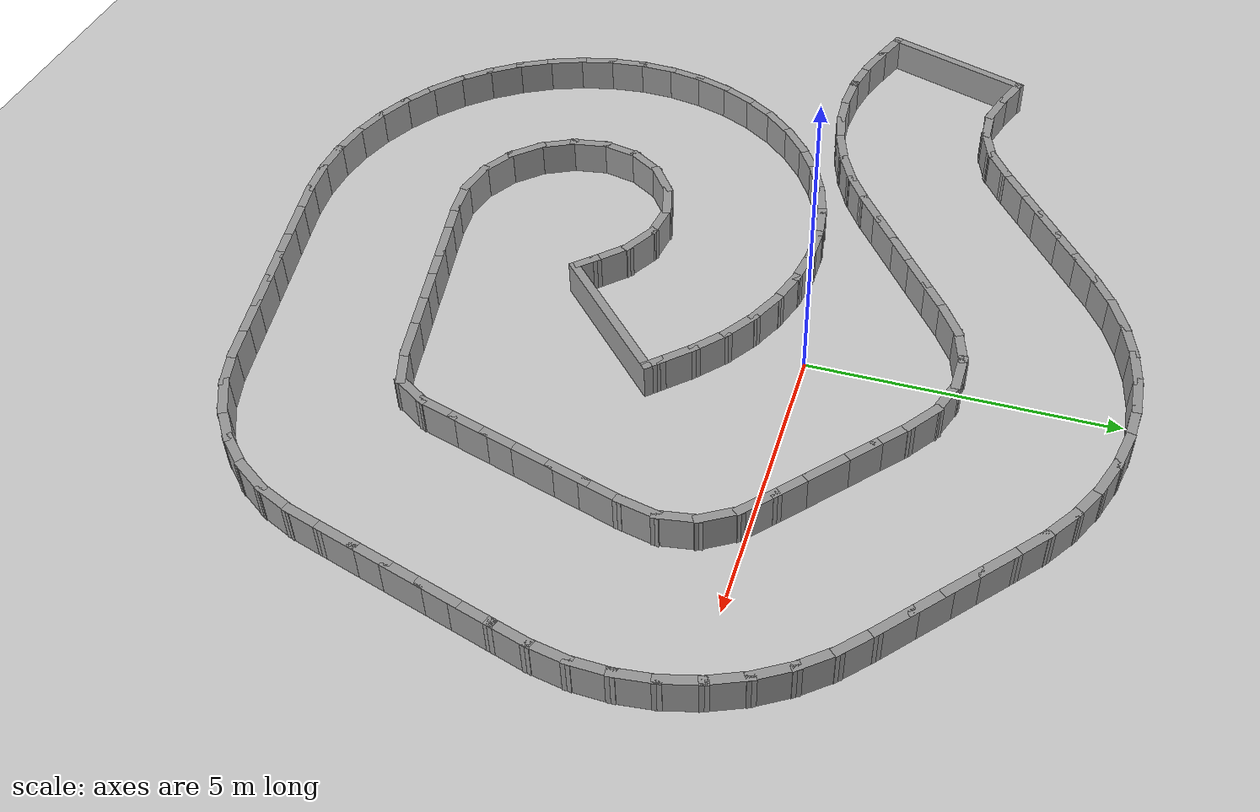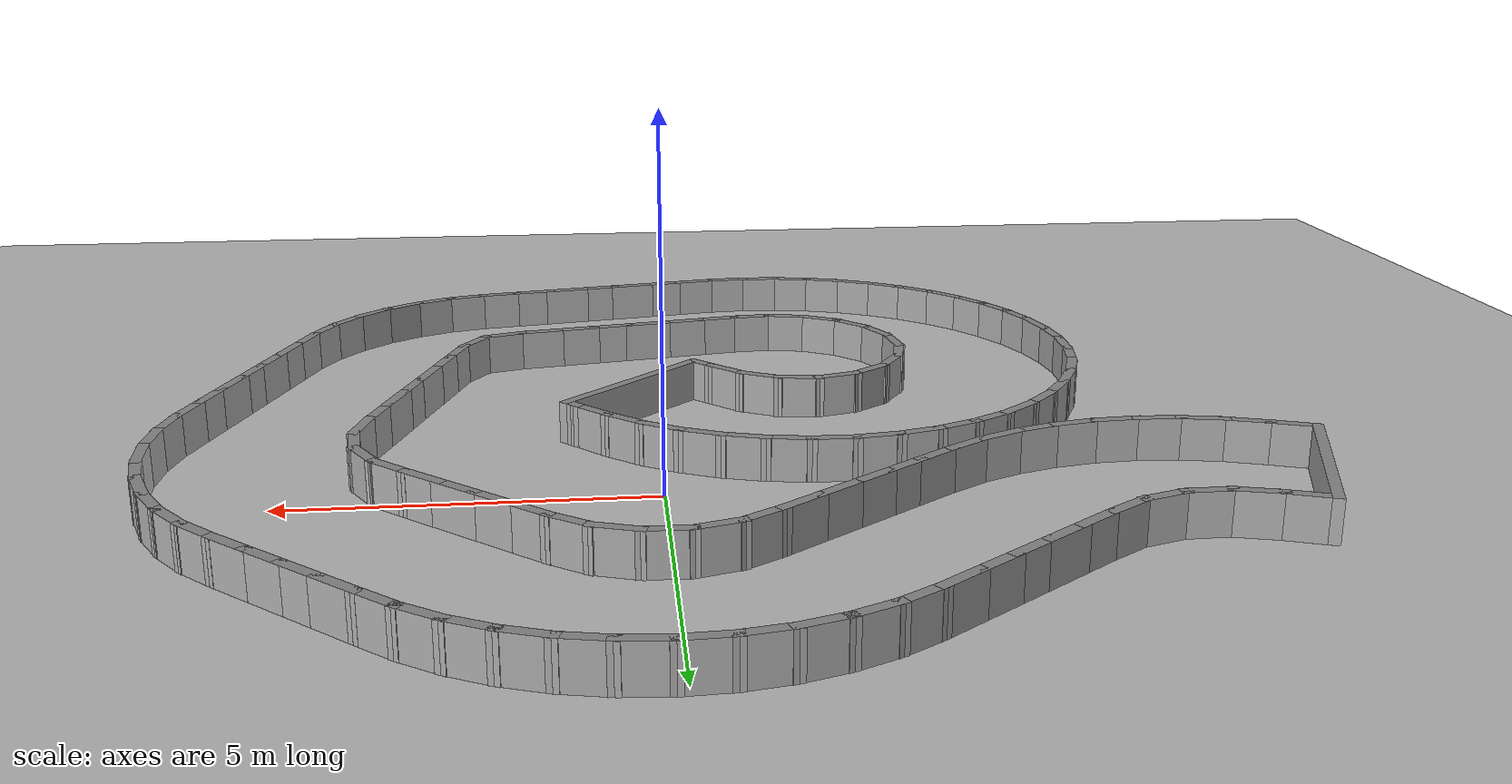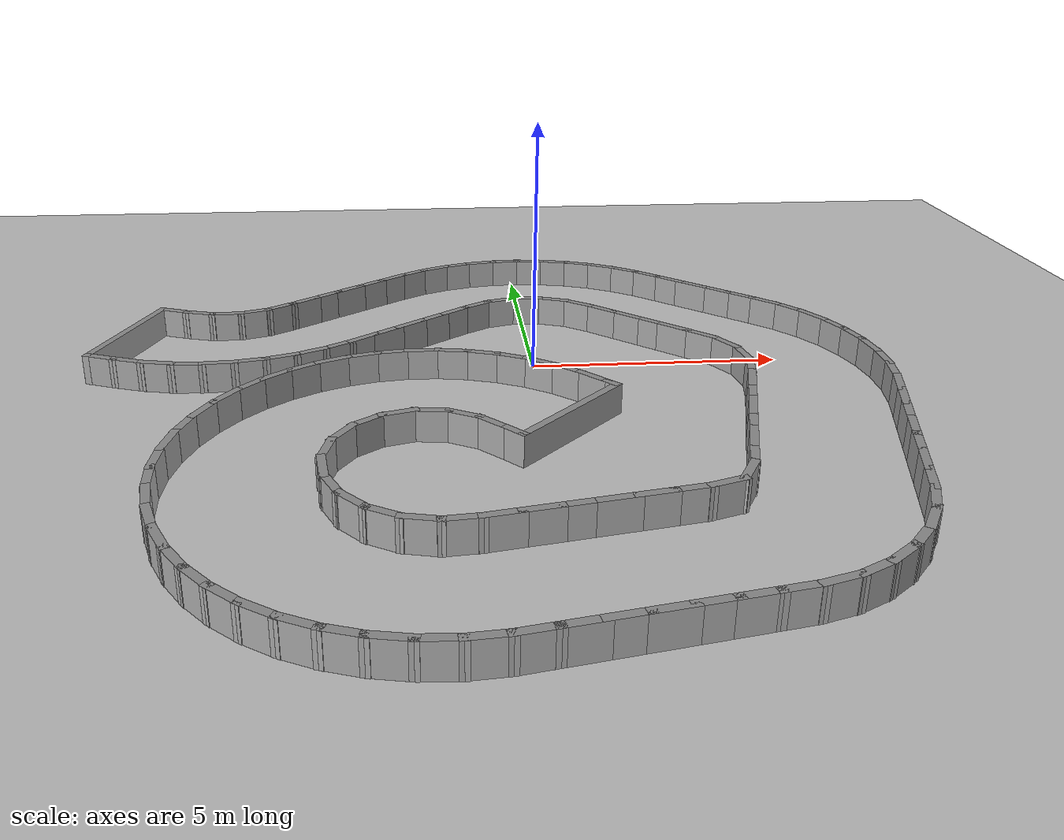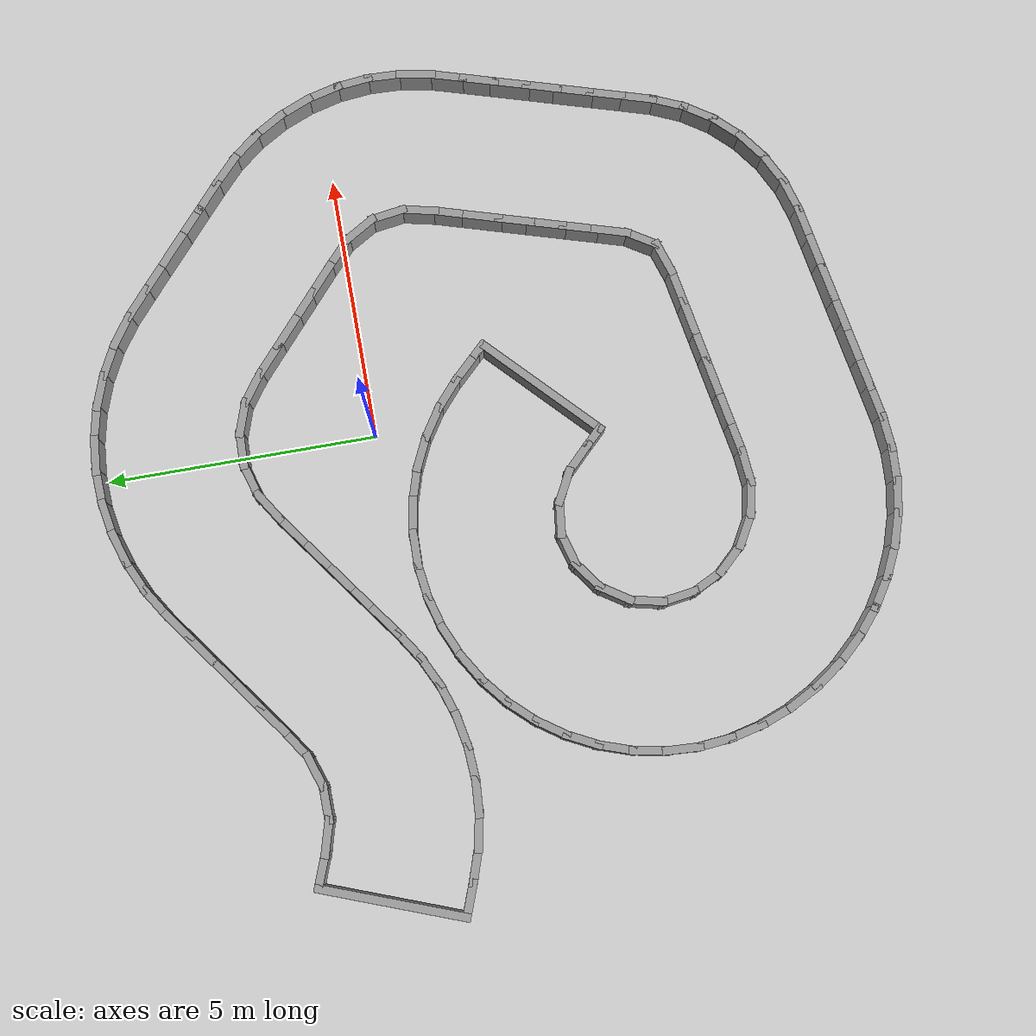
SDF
<?xml version="1.0" ?>
<sdf version='1.7'>
  <world name='default'>
    <plugin name='gazebo_ros_state' filename='libgazebo_ros_state.so'>
      <ros>
        <namespace>/</namespace>
      </ros>
      <update_rate>1000.0</update_rate>
    </plugin>

    <light name='sun' type='directional'>
      <cast_shadows>1</cast_shadows>
      <pose>0 0 10 0 -0 0</pose>
      <diffuse>0.8 0.8 0.8 1</diffuse>
      <specular>0.2 0.2 0.2 1</specular>
      <attenuation>
        <range>1000</range>
        <constant>0.9</constant>
        <linear>0.01</linear>
        <quadratic>0.001</quadratic>
      </attenuation>
      <direction>-0.5 0.1 -0.9</direction>
      <spot>
        <inner_angle>0</inner_angle>
        <outer_angle>0</outer_angle>
        <falloff>0</falloff>
      </spot>
    </light>
    <model name='ground_plane'>
      <static>1</static>
      <link name='link'>
        <collision name='collision'>
          <geometry>
            <plane>
              <normal>0 0 1</normal>
              <size>100 100</size>
            </plane>
          </geometry>
          <surface>
            <friction>
              <ode>
                <mu>100</mu>
                <mu2>50</mu2>
              </ode>
              <torsional>
                <ode/>
              </torsional>
            </friction>
            <contact>
              <ode/>
            </contact>
            <bounce/>
          </surface>
          <max_contacts>10</max_contacts>
        </collision>
        <visual name='visual'>
          <cast_shadows>0</cast_shadows>
          <geometry>
            <plane>
              <normal>0 0 1</normal>
              <size>100 100</size>
            </plane>
          </geometry>
          <material>
            <script>
              <uri>file://media/materials/scripts/gazebo.material</uri>
              <name>Gazebo/Grey</name>
            </script>
          </material>
        </visual>
        <self_collide>0</self_collide>
        <enable_wind>0</enable_wind>
        <kinematic>0</kinematic>
      </link>
    </model>
    <gravity>0 0 -9.8</gravity>
    <magnetic_field>6e-06 2.3e-05 -4.2e-05</magnetic_field>
    <atmosphere type='adiabatic'/>
    <physics type='ode'>
      <max_step_size>0.001</max_step_size>
      <real_time_factor>1</real_time_factor>
      <real_time_update_rate>1000</real_time_update_rate>
    </physics>
    <scene>
      <ambient>0.4 0.4 0.4 1</ambient>
      <background>0.7 0.7 0.7 1</background>
      <shadows>1</shadows>
    </scene>
    <audio>
      <device>default</device>
    </audio>
    <wind/>
    <spherical_coordinates>
      <surface_model>EARTH_WGS84</surface_model>
      <latitude_deg>0</latitude_deg>
      <longitude_deg>0</longitude_deg>
      <elevation>0</elevation>
      <heading_deg>0</heading_deg>
    </spherical_coordinates>
  <model name='rand_turn_10'>
    <pose>0 0 0 0 -0 0</pose>
    <link name='Wall_0'>
      <collision name='Wall_0_Collision'>
        <geometry><box><size>0.7500 0.1500 0.6000</size></box></geometry>
        <pose>0 0 0.3000 0 -0 0</pose>
      </collision>
      <visual name='Wall_0_Visual'>
        <pose>0 0 0.3000 0 -0 0</pose>
        <geometry><box><size>0.7500 0.1500 0.6000</size></box></geometry>
        <material>
          <script>
            <uri>file://media/materials/scripts/gazebo.material</uri>
            <name>Gazebo/Grey</name>
          </script>
          <ambient>1 1 1 1</ambient>
        </material>
      </visual>
      <pose>-7.6169 2.1796 0 0 -0 -0.35750</pose>
    </link>
    <link name='Wall_1'>
      <collision name='Wall_1_Collision'>
        <geometry><box><size>0.7483 0.1500 0.6000</size></box></geometry>
        <pose>0 0 0.3000 0 -0 0</pose>
      </collision>
      <visual name='Wall_1_Visual'>
        <pose>0 0 0.3000 0 -0 0</pose>
        <geometry><box><size>0.7483 0.1500 0.6000</size></box></geometry>
        <material>
          <script>
            <uri>file://media/materials/scripts/gazebo.material</uri>
            <name>Gazebo/Grey</name>
          </script>
          <ambient>1 1 1 1</ambient>
        </material>
      </visual>
      <pose>-7.0479 1.9939 0 0 -0 -0.27353</pose>
    </link>
    <link name='Wall_2'>
      <collision name='Wall_2_Collision'>
        <geometry><box><size>0.7478 0.1500 0.6000</size></box></geometry>
        <pose>0 0 0.3000 0 -0 0</pose>
      </collision>
      <visual name='Wall_2_Visual'>
        <pose>0 0 0.3000 0 -0 0</pose>
        <geometry><box><size>0.7478 0.1500 0.6000</size></box></geometry>
        <material>
          <script>
            <uri>file://media/materials/scripts/gazebo.material</uri>
            <name>Gazebo/Grey</name>
          </script>
          <ambient>1 1 1 1</ambient>
        </material>
      </visual>
      <pose>-6.4610 1.9186 0 0 -0 0.01854</pose>
    </link>
    <link name='Wall_3'>
      <collision name='Wall_3_Collision'>
        <geometry><box><size>0.7478 0.1500 0.6000</size></box></geometry>
        <pose>0 0 0.3000 0 -0 0</pose>
      </collision>
      <visual name='Wall_3_Visual'>
        <pose>0 0 0.3000 0 -0 0</pose>
        <geometry><box><size>0.7478 0.1500 0.6000</size></box></geometry>
        <material>
          <script>
            <uri>file://media/materials/scripts/gazebo.material</uri>
            <name>Gazebo/Grey</name>
          </script>
          <ambient>1 1 1 1</ambient>
        </material>
      </visual>
      <pose>-5.8784 2.0180 0 0 -0 0.31936</pose>
    </link>
    <link name='Wall_4'>
      <collision name='Wall_4_Collision'>
        <geometry><box><size>0.7491 0.1500 0.6000</size></box></geometry>
        <pose>0 0 0.3000 0 -0 0</pose>
      </collision>
      <visual name='Wall_4_Visual'>
        <pose>0 0 0.3000 0 -0 0</pose>
        <geometry><box><size>0.7491 0.1500 0.6000</size></box></geometry>
        <material>
          <script>
            <uri>file://media/materials/scripts/gazebo.material</uri>
            <name>Gazebo/Grey</name>
          </script>
          <ambient>1 1 1 1</ambient>
        </material>
      </visual>
      <pose>-5.3456 2.2783 0 0 -0 0.58934</pose>
    </link>
    <link name='Wall_5'>
      <collision name='Wall_5_Collision'>
        <geometry><box><size>0.7500 0.1500 0.6000</size></box></geometry>
        <pose>0 0 0.3000 0 -0 0</pose>
      </collision>
      <visual name='Wall_5_Visual'>
        <pose>0 0 0.3000 0 -0 0</pose>
        <geometry><box><size>0.7500 0.1500 0.6000</size></box></geometry>
        <material>
          <script>
            <uri>file://media/materials/scripts/gazebo.material</uri>
            <name>Gazebo/Grey</name>
          </script>
          <ambient>1 1 1 1</ambient>
        </material>
      </visual>
      <pose>-4.8548 2.6224 0 0 -0 0.63349</pose>
    </link>
    <link name='Wall_6'>
      <collision name='Wall_6_Collision'>
        <geometry><box><size>0.7500 0.1500 0.6000</size></box></geometry>
        <pose>0 0 0.3000 0 -0 0</pose>
      </collision>
      <visual name='Wall_6_Visual'>
        <pose>0 0 0.3000 0 -0 0</pose>
        <geometry><box><size>0.7500 0.1500 0.6000</size></box></geometry>
        <material>
          <script>
            <uri>file://media/materials/scripts/gazebo.material</uri>
            <name>Gazebo/Grey</name>
          </script>
          <ambient>1 1 1 1</ambient>
        </material>
      </visual>
      <pose>-4.3712 2.9776 0 0 -0 0.63349</pose>
    </link>
    <link name='Wall_7'>
      <collision name='Wall_7_Collision'>
        <geometry><box><size>0.7500 0.1500 0.6000</size></box></geometry>
        <pose>0 0 0.3000 0 -0 0</pose>
      </collision>
      <visual name='Wall_7_Visual'>
        <pose>0 0 0.3000 0 -0 0</pose>
        <geometry><box><size>0.7500 0.1500 0.6000</size></box></geometry>
        <material>
          <script>
            <uri>file://media/materials/scripts/gazebo.material</uri>
            <name>Gazebo/Grey</name>
          </script>
          <ambient>1 1 1 1</ambient>
        </material>
      </visual>
      <pose>-3.8876 3.3327 0 0 -0 0.63349</pose>
    </link>
    <link name='Wall_8'>
      <collision name='Wall_8_Collision'>
        <geometry><box><size>0.7500 0.1500 0.6000</size></box></geometry>
        <pose>0 0 0.3000 0 -0 0</pose>
      </collision>
      <visual name='Wall_8_Visual'>
        <pose>0 0 0.3000 0 -0 0</pose>
        <geometry><box><size>0.7500 0.1500 0.6000</size></box></geometry>
        <material>
          <script>
            <uri>file://media/materials/scripts/gazebo.material</uri>
            <name>Gazebo/Grey</name>
          </script>
          <ambient>1 1 1 1</ambient>
        </material>
      </visual>
      <pose>-3.4040 3.6879 0 0 -0 0.63349</pose>
    </link>
    <link name='Wall_9'>
      <collision name='Wall_9_Collision'>
        <geometry><box><size>0.7500 0.1500 0.6000</size></box></geometry>
        <pose>0 0 0.3000 0 -0 0</pose>
      </collision>
      <visual name='Wall_9_Visual'>
        <pose>0 0 0.3000 0 -0 0</pose>
        <geometry><box><size>0.7500 0.1500 0.6000</size></box></geometry>
        <material>
          <script>
            <uri>file://media/materials/scripts/gazebo.material</uri>
            <name>Gazebo/Grey</name>
          </script>
          <ambient>1 1 1 1</ambient>
        </material>
      </visual>
      <pose>-2.9204 4.0431 0 0 -0 0.63331</pose>
    </link>
    <link name='Wall_10'>
      <collision name='Wall_10_Collision'>
        <geometry><box><size>0.7496 0.1500 0.6000</size></box></geometry>
        <pose>0 0 0.3000 0 -0 0</pose>
      </collision>
      <visual name='Wall_10_Visual'>
        <pose>0 0 0.3000 0 -0 0</pose>
        <geometry><box><size>0.7496 0.1500 0.6000</size></box></geometry>
        <material>
          <script>
            <uri>file://media/materials/scripts/gazebo.material</uri>
            <name>Gazebo/Grey</name>
          </script>
          <ambient>1 1 1 1</ambient>
        </material>
      </visual>
      <pose>-2.4254 4.3810 0 0 -0 0.56464</pose>
    </link>
    <link name='Wall_11'>
      <collision name='Wall_11_Collision'>
        <geometry><box><size>0.7495 0.1500 0.6000</size></box></geometry>
        <pose>0 0 0.3000 0 -0 0</pose>
      </collision>
      <visual name='Wall_11_Visual'>
        <pose>0 0 0.3000 0 -0 0</pose>
        <geometry><box><size>0.7495 0.1500 0.6000</size></box></geometry>
        <material>
          <script>
            <uri>file://media/materials/scripts/gazebo.material</uri>
            <name>Gazebo/Grey</name>
          </script>
          <ambient>1 1 1 1</ambient>
        </material>
      </visual>
      <pose>-1.9003 4.6679 0 0 -0 0.43535</pose>
    </link>
    <link name='Wall_12'>
      <collision name='Wall_12_Collision'>
        <geometry><box><size>0.7496 0.1500 0.6000</size></box></geometry>
        <pose>0 0 0.3000 0 -0 0</pose>
      </collision>
      <visual name='Wall_12_Visual'>
        <pose>0 0 0.3000 0 -0 0</pose>
        <geometry><box><size>0.7496 0.1500 0.6000</size></box></geometry>
        <material>
          <script>
            <uri>file://media/materials/scripts/gazebo.material</uri>
            <name>Gazebo/Grey</name>
          </script>
          <ambient>1 1 1 1</ambient>
        </material>
      </visual>
      <pose>-1.3426 4.8845 0 0 -0 0.30587</pose>
    </link>
    <link name='Wall_13'>
      <collision name='Wall_13_Collision'>
        <geometry><box><size>0.7496 0.1500 0.6000</size></box></geometry>
        <pose>0 0 0.3000 0 -0 0</pose>
      </collision>
      <visual name='Wall_13_Visual'>
        <pose>0 0 0.3000 0 -0 0</pose>
        <geometry><box><size>0.7496 0.1500 0.6000</size></box></geometry>
        <material>
          <script>
            <uri>file://media/materials/scripts/gazebo.material</uri>
            <name>Gazebo/Grey</name>
          </script>
          <ambient>1 1 1 1</ambient>
        </material>
      </visual>
      <pose>-0.7616 5.0270 0 0 -0 0.17493</pose>
    </link>
    <link name='Wall_14'>
      <collision name='Wall_14_Collision'>
        <geometry><box><size>0.7495 0.1500 0.6000</size></box></geometry>
        <pose>0 0 0.3000 0 -0 0</pose>
      </collision>
      <visual name='Wall_14_Visual'>
        <pose>0 0 0.3000 0 -0 0</pose>
        <geometry><box><size>0.7495 0.1500 0.6000</size></box></geometry>
        <material>
          <script>
            <uri>file://media/materials/scripts/gazebo.material</uri>
            <name>Gazebo/Grey</name>
          </script>
          <ambient>1 1 1 1</ambient>
        </material>
      </visual>
      <pose>-0.1669 5.0926 0 0 -0 0.04497</pose>
    </link>
    <link name='Wall_15'>
      <collision name='Wall_15_Collision'>
        <geometry><box><size>0.7495 0.1500 0.6000</size></box></geometry>
        <pose>0 0 0.3000 0 -0 0</pose>
      </collision>
      <visual name='Wall_15_Visual'>
        <pose>0 0 0.3000 0 -0 0</pose>
        <geometry><box><size>0.7495 0.1500 0.6000</size></box></geometry>
        <material>
          <script>
            <uri>file://media/materials/scripts/gazebo.material</uri>
            <name>Gazebo/Grey</name>
          </script>
          <ambient>1 1 1 1</ambient>
        </material>
      </visual>
      <pose>0.4313 5.0808 0 0 -0 -0.08451</pose>
    </link>
    <link name='Wall_16'>
      <collision name='Wall_16_Collision'>
        <geometry><box><size>0.7496 0.1500 0.6000</size></box></geometry>
        <pose>0 0 0.3000 0 -0 0</pose>
      </collision>
      <visual name='Wall_16_Visual'>
        <pose>0 0 0.3000 0 -0 0</pose>
        <geometry><box><size>0.7496 0.1500 0.6000</size></box></geometry>
        <material>
          <script>
            <uri>file://media/materials/scripts/gazebo.material</uri>
            <name>Gazebo/Grey</name>
          </script>
          <ambient>1 1 1 1</ambient>
        </material>
      </visual>
      <pose>1.0229 4.9918 0 0 -0 -0.21422</pose>
    </link>
    <link name='Wall_17'>
      <collision name='Wall_17_Collision'>
        <geometry><box><size>0.7496 0.1500 0.6000</size></box></geometry>
        <pose>0 0 0.3000 0 -0 0</pose>
      </collision>
      <visual name='Wall_17_Visual'>
        <pose>0 0 0.3000 0 -0 0</pose>
        <geometry><box><size>0.7496 0.1500 0.6000</size></box></geometry>
        <material>
          <script>
            <uri>file://media/materials/scripts/gazebo.material</uri>
            <name>Gazebo/Grey</name>
          </script>
          <ambient>1 1 1 1</ambient>
        </material>
      </visual>
      <pose>1.5979 4.8265 0 0 -0 -0.34542</pose>
    </link>
    <link name='Wall_18'>
      <collision name='Wall_18_Collision'>
        <geometry><box><size>0.7495 0.1500 0.6000</size></box></geometry>
        <pose>0 0 0.3000 0 -0 0</pose>
      </collision>
      <visual name='Wall_18_Visual'>
        <pose>0 0 0.3000 0 -0 0</pose>
        <geometry><box><size>0.7495 0.1500 0.6000</size></box></geometry>
        <material>
          <script>
            <uri>file://media/materials/scripts/gazebo.material</uri>
            <name>Gazebo/Grey</name>
          </script>
          <ambient>1 1 1 1</ambient>
        </material>
      </visual>
      <pose>2.1466 4.5880 0 0 -0 -0.47489</pose>
    </link>
    <link name='Wall_19'>
      <collision name='Wall_19_Collision'>
        <geometry><box><size>0.7496 0.1500 0.6000</size></box></geometry>
        <pose>0 0 0.3000 0 -0 0</pose>
      </collision>
      <visual name='Wall_19_Visual'>
        <pose>0 0 0.3000 0 -0 0</pose>
        <geometry><box><size>0.7496 0.1500 0.6000</size></box></geometry>
        <material>
          <script>
            <uri>file://media/materials/scripts/gazebo.material</uri>
            <name>Gazebo/Grey</name>
          </script>
          <ambient>1 1 1 1</ambient>
        </material>
      </visual>
      <pose>2.6599 4.2806 0 0 -0 -0.60436</pose>
    </link>
    <link name='Wall_20'>
      <collision name='Wall_20_Collision'>
        <geometry><box><size>0.7499 0.1500 0.6000</size></box></geometry>
        <pose>0 0 0.3000 0 -0 0</pose>
      </collision>
      <visual name='Wall_20_Visual'>
        <pose>0 0 0.3000 0 -0 0</pose>
        <geometry><box><size>0.7499 0.1500 0.6000</size></box></geometry>
        <material>
          <script>
            <uri>file://media/materials/scripts/gazebo.material</uri>
            <name>Gazebo/Grey</name>
          </script>
          <ambient>1 1 1 1</ambient>
        </material>
      </visual>
      <pose>3.1338 3.9145 0 0 -0 -0.71109</pose>
    </link>
    <link name='Wall_21'>
      <collision name='Wall_21_Collision'>
        <geometry><box><size>0.7500 0.1500 0.6000</size></box></geometry>
        <pose>0 0 0.3000 0 -0 0</pose>
      </collision>
      <visual name='Wall_21_Visual'>
        <pose>0 0 0.3000 0 -0 0</pose>
        <geometry><box><size>0.7500 0.1500 0.6000</size></box></geometry>
        <material>
          <script>
            <uri>file://media/materials/scripts/gazebo.material</uri>
            <name>Gazebo/Grey</name>
          </script>
          <ambient>1 1 1 1</ambient>
        </material>
      </visual>
      <pose>3.5865 3.5207 0 0 -0 -0.72078</pose>
    </link>
    <link name='Wall_22'>
      <collision name='Wall_22_Collision'>
        <geometry><box><size>0.7500 0.1500 0.6000</size></box></geometry>
        <pose>0 0 0.3000 0 -0 0</pose>
      </collision>
      <visual name='Wall_22_Visual'>
        <pose>0 0 0.3000 0 -0 0</pose>
        <geometry><box><size>0.7500 0.1500 0.6000</size></box></geometry>
        <material>
          <script>
            <uri>file://media/materials/scripts/gazebo.material</uri>
            <name>Gazebo/Grey</name>
          </script>
          <ambient>1 1 1 1</ambient>
        </material>
      </visual>
      <pose>4.0372 3.1247 0 0 -0 -0.72078</pose>
    </link>
    <link name='Wall_23'>
      <collision name='Wall_23_Collision'>
        <geometry><box><size>0.7500 0.1500 0.6000</size></box></geometry>
        <pose>0 0 0.3000 0 -0 0</pose>
      </collision>
      <visual name='Wall_23_Visual'>
        <pose>0 0 0.3000 0 -0 0</pose>
        <geometry><box><size>0.7500 0.1500 0.6000</size></box></geometry>
        <material>
          <script>
            <uri>file://media/materials/scripts/gazebo.material</uri>
            <name>Gazebo/Grey</name>
          </script>
          <ambient>1 1 1 1</ambient>
        </material>
      </visual>
      <pose>4.4880 2.7287 0 0 -0 -0.72078</pose>
    </link>
    <link name='Wall_24'>
      <collision name='Wall_24_Collision'>
        <geometry><box><size>0.7500 0.1500 0.6000</size></box></geometry>
        <pose>0 0 0.3000 0 -0 0</pose>
      </collision>
      <visual name='Wall_24_Visual'>
        <pose>0 0 0.3000 0 -0 0</pose>
        <geometry><box><size>0.7500 0.1500 0.6000</size></box></geometry>
        <material>
          <script>
            <uri>file://media/materials/scripts/gazebo.material</uri>
            <name>Gazebo/Grey</name>
          </script>
          <ambient>1 1 1 1</ambient>
        </material>
      </visual>
      <pose>4.9388 2.3327 0 0 -0 -0.72078</pose>
    </link>
    <link name='Wall_25'>
      <collision name='Wall_25_Collision'>
        <geometry><box><size>0.7497 0.1500 0.6000</size></box></geometry>
        <pose>0 0 0.3000 0 -0 0</pose>
      </collision>
      <visual name='Wall_25_Visual'>
        <pose>0 0 0.3000 0 -0 0</pose>
        <geometry><box><size>0.7497 0.1500 0.6000</size></box></geometry>
        <material>
          <script>
            <uri>file://media/materials/scripts/gazebo.material</uri>
            <name>Gazebo/Grey</name>
          </script>
          <ambient>1 1 1 1</ambient>
        </material>
      </visual>
      <pose>5.3823 1.9290 0 0 -0 -0.75607</pose>
    </link>
    <link name='Wall_26'>
      <collision name='Wall_26_Collision'>
        <geometry><box><size>0.7495 0.1500 0.6000</size></box></geometry>
        <pose>0 0 0.3000 0 -0 0</pose>
      </collision>
      <visual name='Wall_26_Visual'>
        <pose>0 0 0.3000 0 -0 0</pose>
        <geometry><box><size>0.7495 0.1500 0.6000</size></box></geometry>
        <material>
          <script>
            <uri>file://media/materials/scripts/gazebo.material</uri>
            <name>Gazebo/Grey</name>
          </script>
          <ambient>1 1 1 1</ambient>
        </material>
      </visual>
      <pose>5.7887 1.4901 0 0 -0 -0.89167</pose>
    </link>
    <link name='Wall_27'>
      <collision name='Wall_27_Collision'>
        <geometry><box><size>0.7495 0.1500 0.6000</size></box></geometry>
        <pose>0 0 0.3000 0 -0 0</pose>
      </collision>
      <visual name='Wall_27_Visual'>
        <pose>0 0 0.3000 0 -0 0</pose>
        <geometry><box><size>0.7495 0.1500 0.6000</size></box></geometry>
        <material>
          <script>
            <uri>file://media/materials/scripts/gazebo.material</uri>
            <name>Gazebo/Grey</name>
          </script>
          <ambient>1 1 1 1</ambient>
        </material>
      </visual>
      <pose>6.1300 0.9991 0 0 -0 -1.03518</pose>
    </link>
    <link name='Wall_28'>
      <collision name='Wall_28_Collision'>
        <geometry><box><size>0.7495 0.1500 0.6000</size></box></geometry>
        <pose>0 0 0.3000 0 -0 0</pose>
      </collision>
      <visual name='Wall_28_Visual'>
        <pose>0 0 0.3000 0 -0 0</pose>
        <geometry><box><size>0.7495 0.1500 0.6000</size></box></geometry>
        <material>
          <script>
            <uri>file://media/materials/scripts/gazebo.material</uri>
            <name>Gazebo/Grey</name>
          </script>
          <ambient>1 1 1 1</ambient>
        </material>
      </visual>
      <pose>6.3976 0.4644 0 0 -0 -1.17840</pose>
    </link>
    <link name='Wall_29'>
      <collision name='Wall_29_Collision'>
        <geometry><box><size>0.7495 0.1500 0.6000</size></box></geometry>
        <pose>0 0 0.3000 0 -0 0</pose>
      </collision>
      <visual name='Wall_29_Visual'>
        <pose>0 0 0.3000 0 -0 0</pose>
        <geometry><box><size>0.7495 0.1500 0.6000</size></box></geometry>
        <material>
          <script>
            <uri>file://media/materials/scripts/gazebo.material</uri>
            <name>Gazebo/Grey</name>
          </script>
          <ambient>1 1 1 1</ambient>
        </material>
      </visual>
      <pose>6.5862 -0.1031 0 0 -0 -1.32133</pose>
    </link>
    <link name='Wall_30'>
      <collision name='Wall_30_Collision'>
        <geometry><box><size>0.7494 0.1500 0.6000</size></box></geometry>
        <pose>0 0 0.3000 0 -0 0</pose>
      </collision>
      <visual name='Wall_30_Visual'>
        <pose>0 0 0.3000 0 -0 0</pose>
        <geometry><box><size>0.7494 0.1500 0.6000</size></box></geometry>
        <material>
          <script>
            <uri>file://media/materials/scripts/gazebo.material</uri>
            <name>Gazebo/Grey</name>
          </script>
          <ambient>1 1 1 1</ambient>
        </material>
      </visual>
      <pose>6.6921 -0.6915 0 0 -0 -1.46426</pose>
    </link>
    <link name='Wall_31'>
      <collision name='Wall_31_Collision'>
        <geometry><box><size>0.7494 0.1500 0.6000</size></box></geometry>
        <pose>0 0 0.3000 0 -0 0</pose>
      </collision>
      <visual name='Wall_31_Visual'>
        <pose>0 0 0.3000 0 -0 0</pose>
        <geometry><box><size>0.7494 0.1500 0.6000</size></box></geometry>
        <material>
          <script>
            <uri>file://media/materials/scripts/gazebo.material</uri>
            <name>Gazebo/Grey</name>
          </script>
          <ambient>1 1 1 1</ambient>
        </material>
      </visual>
      <pose>6.7131 -1.2891 0 0 -0 -1.60719</pose>
    </link>
    <link name='Wall_32'>
      <collision name='Wall_32_Collision'>
        <geometry><box><size>0.7494 0.1500 0.6000</size></box></geometry>
        <pose>0 0 0.3000 0 -0 0</pose>
      </collision>
      <visual name='Wall_32_Visual'>
        <pose>0 0 0.3000 0 -0 0</pose>
        <geometry><box><size>0.7494 0.1500 0.6000</size></box></geometry>
        <material>
          <script>
            <uri>file://media/materials/scripts/gazebo.material</uri>
            <name>Gazebo/Grey</name>
          </script>
          <ambient>1 1 1 1</ambient>
        </material>
      </visual>
      <pose>6.6487 -1.8835 0 0 -0 -1.75019</pose>
    </link>
    <link name='Wall_33'>
      <collision name='Wall_33_Collision'>
        <geometry><box><size>0.7500 0.1500 0.6000</size></box></geometry>
        <pose>0 0 0.3000 0 -0 0</pose>
      </collision>
      <visual name='Wall_33_Visual'>
        <pose>0 0 0.3000 0 -0 0</pose>
        <geometry><box><size>0.7500 0.1500 0.6000</size></box></geometry>
        <material>
          <script>
            <uri>file://media/materials/scripts/gazebo.material</uri>
            <name>Gazebo/Grey</name>
          </script>
          <ambient>1 1 1 1</ambient>
        </material>
      </visual>
      <pose>6.5111 -2.4663 0 0 -0 -1.85487</pose>
    </link>
    <link name='Wall_34'>
      <collision name='Wall_34_Collision'>
        <geometry><box><size>0.7500 0.1500 0.6000</size></box></geometry>
        <pose>0 0 0.3000 0 -0 0</pose>
      </collision>
      <visual name='Wall_34_Visual'>
        <pose>0 0 0.3000 0 -0 0</pose>
        <geometry><box><size>0.7500 0.1500 0.6000</size></box></geometry>
        <material>
          <script>
            <uri>file://media/materials/scripts/gazebo.material</uri>
            <name>Gazebo/Grey</name>
          </script>
          <ambient>1 1 1 1</ambient>
        </material>
      </visual>
      <pose>6.3416 -3.0419 0 0 -0 -1.85970</pose>
    </link>
    <link name='Wall_35'>
      <collision name='Wall_35_Collision'>
        <geometry><box><size>0.7500 0.1500 0.6000</size></box></geometry>
        <pose>0 0 0.3000 0 -0 0</pose>
      </collision>
      <visual name='Wall_35_Visual'>
        <pose>0 0 0.3000 0 -0 0</pose>
        <geometry><box><size>0.7500 0.1500 0.6000</size></box></geometry>
        <material>
          <script>
            <uri>file://media/materials/scripts/gazebo.material</uri>
            <name>Gazebo/Grey</name>
          </script>
          <ambient>1 1 1 1</ambient>
        </material>
      </visual>
      <pose>6.1706 -3.6170 0 0 -0 -1.85970</pose>
    </link>
    <link name='Wall_36'>
      <collision name='Wall_36_Collision'>
        <geometry><box><size>0.7500 0.1500 0.6000</size></box></geometry>
        <pose>0 0 0.3000 0 -0 0</pose>
      </collision>
      <visual name='Wall_36_Visual'>
        <pose>0 0 0.3000 0 -0 0</pose>
        <geometry><box><size>0.7500 0.1500 0.6000</size></box></geometry>
        <material>
          <script>
            <uri>file://media/materials/scripts/gazebo.material</uri>
            <name>Gazebo/Grey</name>
          </script>
          <ambient>1 1 1 1</ambient>
        </material>
      </visual>
      <pose>5.9997 -4.1921 0 0 -0 -1.85970</pose>
    </link>
    <link name='Wall_37'>
      <collision name='Wall_37_Collision'>
        <geometry><box><size>0.7500 0.1500 0.6000</size></box></geometry>
        <pose>0 0 0.3000 0 -0 0</pose>
      </collision>
      <visual name='Wall_37_Visual'>
        <pose>0 0 0.3000 0 -0 0</pose>
        <geometry><box><size>0.7500 0.1500 0.6000</size></box></geometry>
        <material>
          <script>
            <uri>file://media/materials/scripts/gazebo.material</uri>
            <name>Gazebo/Grey</name>
          </script>
          <ambient>1 1 1 1</ambient>
        </material>
      </visual>
      <pose>5.8287 -4.7673 0 0 -0 -1.85970</pose>
    </link>
    <link name='Wall_38'>
      <collision name='Wall_38_Collision'>
        <geometry><box><size>0.7500 0.1500 0.6000</size></box></geometry>
        <pose>0 0 0.3000 0 -0 0</pose>
      </collision>
      <visual name='Wall_38_Visual'>
        <pose>0 0 0.3000 0 -0 0</pose>
        <geometry><box><size>0.7500 0.1500 0.6000</size></box></geometry>
        <material>
          <script>
            <uri>file://media/materials/scripts/gazebo.material</uri>
            <name>Gazebo/Grey</name>
          </script>
          <ambient>1 1 1 1</ambient>
        </material>
      </visual>
      <pose>5.6578 -5.3424 0 0 -0 -1.85970</pose>
    </link>
    <link name='Wall_39'>
      <collision name='Wall_39_Collision'>
        <geometry><box><size>0.7500 0.1500 0.6000</size></box></geometry>
        <pose>0 0 0.3000 0 -0 0</pose>
      </collision>
      <visual name='Wall_39_Visual'>
        <pose>0 0 0.3000 0 -0 0</pose>
        <geometry><box><size>0.7500 0.1500 0.6000</size></box></geometry>
        <material>
          <script>
            <uri>file://media/materials/scripts/gazebo.material</uri>
            <name>Gazebo/Grey</name>
          </script>
          <ambient>1 1 1 1</ambient>
        </material>
      </visual>
      <pose>5.4857 -5.9172 0 0 -0 -1.86383</pose>
    </link>
    <link name='Wall_40'>
      <collision name='Wall_40_Collision'>
        <geometry><box><size>0.7491 0.1500 0.6000</size></box></geometry>
        <pose>0 0 0.3000 0 -0 0</pose>
      </collision>
      <visual name='Wall_40_Visual'>
        <pose>0 0 0.3000 0 -0 0</pose>
        <geometry><box><size>0.7491 0.1500 0.6000</size></box></geometry>
        <material>
          <script>
            <uri>file://media/materials/scripts/gazebo.material</uri>
            <name>Gazebo/Grey</name>
          </script>
          <ambient>1 1 1 1</ambient>
        </material>
      </visual>
      <pose>5.2800 -6.4793 0 0 -0 -1.97924</pose>
    </link>
    <link name='Wall_41'>
      <collision name='Wall_41_Collision'>
        <geometry><box><size>0.7492 0.1500 0.6000</size></box></geometry>
        <pose>0 0 0.3000 0 -0 0</pose>
      </collision>
      <visual name='Wall_41_Visual'>
        <pose>0 0 0.3000 0 -0 0</pose>
        <geometry><box><size>0.7492 0.1500 0.6000</size></box></geometry>
        <material>
          <script>
            <uri>file://media/materials/scripts/gazebo.material</uri>
            <name>Gazebo/Grey</name>
          </script>
          <ambient>1 1 1 1</ambient>
        </material>
      </visual>
      <pose>4.9963 -7.0044 0 0 -0 -2.15323</pose>
    </link>
    <link name='Wall_42'>
      <collision name='Wall_42_Collision'>
        <geometry><box><size>0.7492 0.1500 0.6000</size></box></geometry>
        <pose>0 0 0.3000 0 -0 0</pose>
      </collision>
      <visual name='Wall_42_Visual'>
        <pose>0 0 0.3000 0 -0 0</pose>
        <geometry><box><size>0.7492 0.1500 0.6000</size></box></geometry>
        <material>
          <script>
            <uri>file://media/materials/scripts/gazebo.material</uri>
            <name>Gazebo/Grey</name>
          </script>
          <ambient>1 1 1 1</ambient>
        </material>
      </visual>
      <pose>4.6249 -7.4716 0 0 -0 -2.33162</pose>
    </link>
    <link name='Wall_43'>
      <collision name='Wall_43_Collision'>
        <geometry><box><size>0.7491 0.1500 0.6000</size></box></geometry>
        <pose>0 0 0.3000 0 -0 0</pose>
      </collision>
      <visual name='Wall_43_Visual'>
        <pose>0 0 0.3000 0 -0 0</pose>
        <geometry><box><size>0.7491 0.1500 0.6000</size></box></geometry>
        <material>
          <script>
            <uri>file://media/materials/scripts/gazebo.material</uri>
            <name>Gazebo/Grey</name>
          </script>
          <ambient>1 1 1 1</ambient>
        </material>
      </visual>
      <pose>4.1773 -7.8665 0 0 -0 -2.50584</pose>
    </link>
    <link name='Wall_44'>
      <collision name='Wall_44_Collision'>
        <geometry><box><size>0.7492 0.1500 0.6000</size></box></geometry>
        <pose>0 0 0.3000 0 -0 0</pose>
      </collision>
      <visual name='Wall_44_Visual'>
        <pose>0 0 0.3000 0 -0 0</pose>
        <geometry><box><size>0.7492 0.1500 0.6000</size></box></geometry>
        <material>
          <script>
            <uri>file://media/materials/scripts/gazebo.material</uri>
            <name>Gazebo/Grey</name>
          </script>
          <ambient>1 1 1 1</ambient>
        </material>
      </visual>
      <pose>3.6680 -8.1778 0 0 -0 -2.68001</pose>
    </link>
    <link name='Wall_45'>
      <collision name='Wall_45_Collision'>
        <geometry><box><size>0.7492 0.1500 0.6000</size></box></geometry>
        <pose>0 0 0.3000 0 -0 0</pose>
      </collision>
      <visual name='Wall_45_Visual'>
        <pose>0 0 0.3000 0 -0 0</pose>
        <geometry><box><size>0.7492 0.1500 0.6000</size></box></geometry>
        <material>
          <script>
            <uri>file://media/materials/scripts/gazebo.material</uri>
            <name>Gazebo/Grey</name>
          </script>
          <ambient>1 1 1 1</ambient>
        </material>
      </visual>
      <pose>3.1121 -8.3951 0 0 -0 -2.85792</pose>
    </link>
    <link name='Wall_46'>
      <collision name='Wall_46_Collision'>
        <geometry><box><size>0.7500 0.1500 0.6000</size></box></geometry>
        <pose>0 0 0.3000 0 -0 0</pose>
      </collision>
      <visual name='Wall_46_Visual'>
        <pose>0 0 0.3000 0 -0 0</pose>
        <geometry><box><size>0.7500 0.1500 0.6000</size></box></geometry>
        <material>
          <script>
            <uri>file://media/materials/scripts/gazebo.material</uri>
            <name>Gazebo/Grey</name>
          </script>
          <ambient>1 1 1 1</ambient>
        </material>
      </visual>
      <pose>2.5292 -8.5320 0 0 -0 -2.96390</pose>
    </link>
    <link name='Wall_47'>
      <collision name='Wall_47_Collision'>
        <geometry><box><size>0.7500 0.1500 0.6000</size></box></geometry>
        <pose>0 0 0.3000 0 -0 0</pose>
      </collision>
      <visual name='Wall_47_Visual'>
        <pose>0 0 0.3000 0 -0 0</pose>
        <geometry><box><size>0.7500 0.1500 0.6000</size></box></geometry>
        <material>
          <script>
            <uri>file://media/materials/scripts/gazebo.material</uri>
            <name>Gazebo/Grey</name>
          </script>
          <ambient>1 1 1 1</ambient>
        </material>
      </visual>
      <pose>1.9385 -8.6374 0 0 -0 -2.96626</pose>
    </link>
    <link name='Wall_48'>
      <collision name='Wall_48_Collision'>
        <geometry><box><size>0.7500 0.1500 0.6000</size></box></geometry>
        <pose>0 0 0.3000 0 -0 0</pose>
      </collision>
      <visual name='Wall_48_Visual'>
        <pose>0 0 0.3000 0 -0 0</pose>
        <geometry><box><size>0.7500 0.1500 0.6000</size></box></geometry>
        <material>
          <script>
            <uri>file://media/materials/scripts/gazebo.material</uri>
            <name>Gazebo/Grey</name>
          </script>
          <ambient>1 1 1 1</ambient>
        </material>
      </visual>
      <pose>1.3477 -8.7420 0 0 -0 -2.96626</pose>
    </link>
    <link name='Wall_49'>
      <collision name='Wall_49_Collision'>
        <geometry><box><size>0.7500 0.1500 0.6000</size></box></geometry>
        <pose>0 0 0.3000 0 -0 0</pose>
      </collision>
      <visual name='Wall_49_Visual'>
        <pose>0 0 0.3000 0 -0 0</pose>
        <geometry><box><size>0.7500 0.1500 0.6000</size></box></geometry>
        <material>
          <script>
            <uri>file://media/materials/scripts/gazebo.material</uri>
            <name>Gazebo/Grey</name>
          </script>
          <ambient>1 1 1 1</ambient>
        </material>
      </visual>
      <pose>0.7569 -8.8467 0 0 -0 -2.96626</pose>
    </link>
    <link name='Wall_50'>
      <collision name='Wall_50_Collision'>
        <geometry><box><size>0.7500 0.1500 0.6000</size></box></geometry>
        <pose>0 0 0.3000 0 -0 0</pose>
      </collision>
      <visual name='Wall_50_Visual'>
        <pose>0 0 0.3000 0 -0 0</pose>
        <geometry><box><size>0.7500 0.1500 0.6000</size></box></geometry>
        <material>
          <script>
            <uri>file://media/materials/scripts/gazebo.material</uri>
            <name>Gazebo/Grey</name>
          </script>
          <ambient>1 1 1 1</ambient>
        </material>
      </visual>
      <pose>0.1661 -8.9513 0 0 -0 -2.96626</pose>
    </link>
    <link name='Wall_51'>
      <collision name='Wall_51_Collision'>
        <geometry><box><size>0.7500 0.1500 0.6000</size></box></geometry>
        <pose>0 0 0.3000 0 -0 0</pose>
      </collision>
      <visual name='Wall_51_Visual'>
        <pose>0 0 0.3000 0 -0 0</pose>
        <geometry><box><size>0.7500 0.1500 0.6000</size></box></geometry>
        <material>
          <script>
            <uri>file://media/materials/scripts/gazebo.material</uri>
            <name>Gazebo/Grey</name>
          </script>
          <ambient>1 1 1 1</ambient>
        </material>
      </visual>
      <pose>-0.4247 -9.0560 0 0 -0 -2.96626</pose>
    </link>
    <link name='Wall_52'>
      <collision name='Wall_52_Collision'>
        <geometry><box><size>0.7500 0.1500 0.6000</size></box></geometry>
        <pose>0 0 0.3000 0 -0 0</pose>
      </collision>
      <visual name='Wall_52_Visual'>
        <pose>0 0 0.3000 0 -0 0</pose>
        <geometry><box><size>0.7500 0.1500 0.6000</size></box></geometry>
        <material>
          <script>
            <uri>file://media/materials/scripts/gazebo.material</uri>
            <name>Gazebo/Grey</name>
          </script>
          <ambient>1 1 1 1</ambient>
        </material>
      </visual>
      <pose>-1.0157 -9.1596 0 0 -0 -2.96981</pose>
    </link>
    <link name='Wall_53'>
      <collision name='Wall_53_Collision'>
        <geometry><box><size>0.7496 0.1500 0.6000</size></box></geometry>
        <pose>0 0 0.3000 0 -0 0</pose>
      </collision>
      <visual name='Wall_53_Visual'>
        <pose>0 0 0.3000 0 -0 0</pose>
        <geometry><box><size>0.7496 0.1500 0.6000</size></box></geometry>
        <material>
          <script>
            <uri>file://media/materials/scripts/gazebo.material</uri>
            <name>Gazebo/Grey</name>
          </script>
          <ambient>1 1 1 1</ambient>
        </material>
      </visual>
      <pose>-1.6101 -9.2348 0 0 -0 -3.06193</pose>
    </link>
    <link name='Wall_54'>
      <collision name='Wall_54_Collision'>
        <geometry><box><size>0.7495 0.1500 0.6000</size></box></geometry>
        <pose>0 0 0.3000 0 -0 0</pose>
      </collision>
      <visual name='Wall_54_Visual'>
        <pose>0 0 0.3000 0 -0 0</pose>
        <geometry><box><size>0.7495 0.1500 0.6000</size></box></geometry>
        <material>
          <script>
            <uri>file://media/materials/scripts/gazebo.material</uri>
            <name>Gazebo/Grey</name>
          </script>
          <ambient>1 1 1 1</ambient>
        </material>
      </visual>
      <pose>-2.2083 -9.2439 0 0 -0 3.09248</pose>
    </link>
    <link name='Wall_55'>
      <collision name='Wall_55_Collision'>
        <geometry><box><size>0.7496 0.1500 0.6000</size></box></geometry>
        <pose>0 0 0.3000 0 -0 0</pose>
      </collision>
      <visual name='Wall_55_Visual'>
        <pose>0 0 0.3000 0 -0 0</pose>
        <geometry><box><size>0.7496 0.1500 0.6000</size></box></geometry>
        <material>
          <script>
            <uri>file://media/materials/scripts/gazebo.material</uri>
            <name>Gazebo/Grey</name>
          </script>
          <ambient>1 1 1 1</ambient>
        </material>
      </visual>
      <pose>-2.8028 -9.1761 0 0 -0 2.96370</pose>
    </link>
    <link name='Wall_56'>
      <collision name='Wall_56_Collision'>
        <geometry><box><size>0.7496 0.1500 0.6000</size></box></geometry>
        <pose>0 0 0.3000 0 -0 0</pose>
      </collision>
      <visual name='Wall_56_Visual'>
        <pose>0 0 0.3000 0 -0 0</pose>
        <geometry><box><size>0.7496 0.1500 0.6000</size></box></geometry>
        <material>
          <script>
            <uri>file://media/materials/scripts/gazebo.material</uri>
            <name>Gazebo/Grey</name>
          </script>
          <ambient>1 1 1 1</ambient>
        </material>
      </visual>
      <pose>-3.3835 -9.0323 0 0 -0 2.83393</pose>
    </link>
    <link name='Wall_57'>
      <collision name='Wall_57_Collision'>
        <geometry><box><size>0.7496 0.1500 0.6000</size></box></geometry>
        <pose>0 0 0.3000 0 -0 0</pose>
      </collision>
      <visual name='Wall_57_Visual'>
        <pose>0 0 0.3000 0 -0 0</pose>
        <geometry><box><size>0.7496 0.1500 0.6000</size></box></geometry>
        <material>
          <script>
            <uri>file://media/materials/scripts/gazebo.material</uri>
            <name>Gazebo/Grey</name>
          </script>
          <ambient>1 1 1 1</ambient>
        </material>
      </visual>
      <pose>-3.9408 -8.8145 0 0 -0 2.70414</pose>
    </link>
    <link name='Wall_58'>
      <collision name='Wall_58_Collision'>
        <geometry><box><size>0.7495 0.1500 0.6000</size></box></geometry>
        <pose>0 0 0.3000 0 -0 0</pose>
      </collision>
      <visual name='Wall_58_Visual'>
        <pose>0 0 0.3000 0 -0 0</pose>
        <geometry><box><size>0.7495 0.1500 0.6000</size></box></geometry>
        <material>
          <script>
            <uri>file://media/materials/scripts/gazebo.material</uri>
            <name>Gazebo/Grey</name>
          </script>
          <ambient>1 1 1 1</ambient>
        </material>
      </visual>
      <pose>-4.4653 -8.5267 0 0 -0 2.57536</pose>
    </link>
    <link name='Wall_59'>
      <collision name='Wall_59_Collision'>
        <geometry><box><size>0.7496 0.1500 0.6000</size></box></geometry>
        <pose>0 0 0.3000 0 -0 0</pose>
      </collision>
      <visual name='Wall_59_Visual'>
        <pose>0 0 0.3000 0 -0 0</pose>
        <geometry><box><size>0.7496 0.1500 0.6000</size></box></geometry>
        <material>
          <script>
            <uri>file://media/materials/scripts/gazebo.material</uri>
            <name>Gazebo/Grey</name>
          </script>
          <ambient>1 1 1 1</ambient>
        </material>
      </visual>
      <pose>-4.9486 -8.1739 0 0 -0 2.44658</pose>
    </link>
    <link name='Wall_60'>
      <collision name='Wall_60_Collision'>
        <geometry><box><size>0.7496 0.1500 0.6000</size></box></geometry>
        <pose>0 0 0.3000 0 -0 0</pose>
      </collision>
      <visual name='Wall_60_Visual'>
        <pose>0 0 0.3000 0 -0 0</pose>
        <geometry><box><size>0.7496 0.1500 0.6000</size></box></geometry>
        <material>
          <script>
            <uri>file://media/materials/scripts/gazebo.material</uri>
            <name>Gazebo/Grey</name>
          </script>
          <ambient>1 1 1 1</ambient>
        </material>
      </visual>
      <pose>-5.3821 -7.7616 0 0 -0 2.31584</pose>
    </link>
    <link name='Wall_61'>
      <collision name='Wall_61_Collision'>
        <geometry><box><size>0.7495 0.1500 0.6000</size></box></geometry>
        <pose>0 0 0.3000 0 -0 0</pose>
      </collision>
      <visual name='Wall_61_Visual'>
        <pose>0 0 0.3000 0 -0 0</pose>
        <geometry><box><size>0.7495 0.1500 0.6000</size></box></geometry>
        <material>
          <script>
            <uri>file://media/materials/scripts/gazebo.material</uri>
            <name>Gazebo/Grey</name>
          </script>
          <ambient>1 1 1 1</ambient>
        </material>
      </visual>
      <pose>-5.7586 -7.2966 0 0 -0 2.18702</pose>
    </link>
    <link name='Wall_62'>
      <collision name='Wall_62_Collision'>
        <geometry><box><size>0.7496 0.1500 0.6000</size></box></geometry>
        <pose>0 0 0.3000 0 -0 0</pose>
      </collision>
      <visual name='Wall_62_Visual'>
        <pose>0 0 0.3000 0 -0 0</pose>
        <geometry><box><size>0.7496 0.1500 0.6000</size></box></geometry>
        <material>
          <script>
            <uri>file://media/materials/scripts/gazebo.material</uri>
            <name>Gazebo/Grey</name>
          </script>
          <ambient>1 1 1 1</ambient>
        </material>
      </visual>
      <pose>-6.0723 -6.7871 0 0 -0 2.05825</pose>
    </link>
    <link name='Wall_63'>
      <collision name='Wall_63_Collision'>
        <geometry><box><size>0.7496 0.1500 0.6000</size></box></geometry>
        <pose>0 0 0.3000 0 -0 0</pose>
      </collision>
      <visual name='Wall_63_Visual'>
        <pose>0 0 0.3000 0 -0 0</pose>
        <geometry><box><size>0.7496 0.1500 0.6000</size></box></geometry>
        <material>
          <script>
            <uri>file://media/materials/scripts/gazebo.material</uri>
            <name>Gazebo/Grey</name>
          </script>
          <ambient>1 1 1 1</ambient>
        </material>
      </visual>
      <pose>-6.3176 -6.2414 0 0 -0 1.92853</pose>
    </link>
    <link name='Wall_64'>
      <collision name='Wall_64_Collision'>
        <geometry><box><size>0.7496 0.1500 0.6000</size></box></geometry>
        <pose>0 0 0.3000 0 -0 0</pose>
      </collision>
      <visual name='Wall_64_Visual'>
        <pose>0 0 0.3000 0 -0 0</pose>
        <geometry><box><size>0.7496 0.1500 0.6000</size></box></geometry>
        <material>
          <script>
            <uri>file://media/materials/scripts/gazebo.material</uri>
            <name>Gazebo/Grey</name>
          </script>
          <ambient>1 1 1 1</ambient>
        </material>
      </visual>
      <pose>-6.4903 -5.6686 0 0 -0 1.79869</pose>
    </link>
    <link name='Wall_65'>
      <collision name='Wall_65_Collision'>
        <geometry><box><size>0.7494 0.1500 0.6000</size></box></geometry>
        <pose>0 0 0.3000 0 -0 0</pose>
      </collision>
      <visual name='Wall_65_Visual'>
        <pose>0 0 0.3000 0 -0 0</pose>
        <geometry><box><size>0.7494 0.1500 0.6000</size></box></geometry>
        <material>
          <script>
            <uri>file://media/materials/scripts/gazebo.material</uri>
            <name>Gazebo/Grey</name>
          </script>
          <ambient>1 1 1 1</ambient>
        </material>
      </visual>
      <pose>-6.5869 -5.0782 0 0 -0 1.66726</pose>
    </link>
    <link name='Wall_66'>
      <collision name='Wall_66_Collision'>
        <geometry><box><size>0.7495 0.1500 0.6000</size></box></geometry>
        <pose>0 0 0.3000 0 -0 0</pose>
      </collision>
      <visual name='Wall_66_Visual'>
        <pose>0 0 0.3000 0 -0 0</pose>
        <geometry><box><size>0.7495 0.1500 0.6000</size></box></geometry>
        <material>
          <script>
            <uri>file://media/materials/scripts/gazebo.material</uri>
            <name>Gazebo/Grey</name>
          </script>
          <ambient>1 1 1 1</ambient>
        </material>
      </visual>
      <pose>-6.6006 -4.4806 0 0 -0 1.51997</pose>
    </link>
    <link name='Wall_67'>
      <collision name='Wall_67_Collision'>
        <geometry><box><size>0.7495 0.1500 0.6000</size></box></geometry>
        <pose>0 0 0.3000 0 -0 0</pose>
      </collision>
      <visual name='Wall_67_Visual'>
        <pose>0 0 0.3000 0 -0 0</pose>
        <geometry><box><size>0.7495 0.1500 0.6000</size></box></geometry>
        <material>
          <script>
            <uri>file://media/materials/scripts/gazebo.material</uri>
            <name>Gazebo/Grey</name>
          </script>
          <ambient>1 1 1 1</ambient>
        </material>
      </visual>
      <pose>-6.5289 -3.8868 0 0 -0 1.38127</pose>
    </link>
    <link name='Wall_68'>
      <collision name='Wall_68_Collision'>
        <geometry><box><size>0.7495 0.1500 0.6000</size></box></geometry>
        <pose>0 0 0.3000 0 -0 0</pose>
      </collision>
      <visual name='Wall_68_Visual'>
        <pose>0 0 0.3000 0 -0 0</pose>
        <geometry><box><size>0.7495 0.1500 0.6000</size></box></geometry>
        <material>
          <script>
            <uri>file://media/materials/scripts/gazebo.material</uri>
            <name>Gazebo/Grey</name>
          </script>
          <ambient>1 1 1 1</ambient>
        </material>
      </visual>
      <pose>-6.3758 -3.3087 0 0 -0 1.24278</pose>
    </link>
    <link name='Wall_69'>
      <collision name='Wall_69_Collision'>
        <geometry><box><size>0.7495 0.1500 0.6000</size></box></geometry>
        <pose>0 0 0.3000 0 -0 0</pose>
      </collision>
      <visual name='Wall_69_Visual'>
        <pose>0 0 0.3000 0 -0 0</pose>
        <geometry><box><size>0.7495 0.1500 0.6000</size></box></geometry>
        <material>
          <script>
            <uri>file://media/materials/scripts/gazebo.material</uri>
            <name>Gazebo/Grey</name>
          </script>
          <ambient>1 1 1 1</ambient>
        </material>
      </visual>
      <pose>-6.1442 -2.7573 0 0 -0 1.10325</pose>
    </link>
    <link name='Wall_70'>
      <collision name='Wall_70_Collision'>
        <geometry><box><size>0.7495 0.1500 0.6000</size></box></geometry>
        <pose>0 0 0.3000 0 -0 0</pose>
      </collision>
      <visual name='Wall_70_Visual'>
        <pose>0 0 0.3000 0 -0 0</pose>
        <geometry><box><size>0.7495 0.1500 0.6000</size></box></geometry>
        <material>
          <script>
            <uri>file://media/materials/scripts/gazebo.material</uri>
            <name>Gazebo/Grey</name>
          </script>
          <ambient>1 1 1 1</ambient>
        </material>
      </visual>
      <pose>-5.8383 -2.2434 0 0 -0 0.96452</pose>
    </link>
    <link name='Wall_71'>
      <collision name='Wall_71_Collision'>
        <geometry><box><size>0.7495 0.1500 0.6000</size></box></geometry>
        <pose>0 0 0.3000 0 -0 0</pose>
      </collision>
      <visual name='Wall_71_Visual'>
        <pose>0 0 0.3000 0 -0 0</pose>
        <geometry><box><size>0.7495 0.1500 0.6000</size></box></geometry>
        <material>
          <script>
            <uri>file://media/materials/scripts/gazebo.material</uri>
            <name>Gazebo/Grey</name>
          </script>
          <ambient>1 1 1 1</ambient>
        </material>
      </visual>
      <pose>-5.4643 -1.7767 0 0 -0 0.82603</pose>
    </link>
    <link name='Wall_72'>
      <collision name='Wall_72_Collision'>
        <geometry><box><size>0.7495 0.1500 0.6000</size></box></geometry>
        <pose>0 0 0.3000 0 -0 0</pose>
      </collision>
      <visual name='Wall_72_Visual'>
        <pose>0 0 0.3000 0 -0 0</pose>
        <geometry><box><size>0.7495 0.1500 0.6000</size></box></geometry>
        <material>
          <script>
            <uri>file://media/materials/scripts/gazebo.material</uri>
            <name>Gazebo/Grey</name>
          </script>
          <ambient>1 1 1 1</ambient>
        </material>
      </visual>
      <pose>-5.0295 -1.3661 0 0 -0 0.68755</pose>
    </link>
    <link name='Wall_73'>
      <collision name='Wall_73_Collision'>
        <geometry><box><size>0.7495 0.1500 0.6000</size></box></geometry>
        <pose>0 0 0.3000 0 -0 0</pose>
      </collision>
      <visual name='Wall_73_Visual'>
        <pose>0 0 0.3000 0 -0 0</pose>
        <geometry><box><size>0.7495 0.1500 0.6000</size></box></geometry>
        <material>
          <script>
            <uri>file://media/materials/scripts/gazebo.material</uri>
            <name>Gazebo/Grey</name>
          </script>
          <ambient>1 1 1 1</ambient>
        </material>
      </visual>
      <pose>-4.5422 -1.0194 0 0 -0 0.54906</pose>
    </link>
    <link name='Wall_74'>
      <collision name='Wall_74_Collision'>
        <geometry><box><size>0.7495 0.1500 0.6000</size></box></geometry>
        <pose>0 0 0.3000 0 -0 0</pose>
      </collision>
      <visual name='Wall_74_Visual'>
        <pose>0 0 0.3000 0 -0 0</pose>
        <geometry><box><size>0.7495 0.1500 0.6000</size></box></geometry>
        <material>
          <script>
            <uri>file://media/materials/scripts/gazebo.material</uri>
            <name>Gazebo/Grey</name>
          </script>
          <ambient>1 1 1 1</ambient>
        </material>
      </visual>
      <pose>-4.0117 -0.7434 0 0 -0 0.41057</pose>
    </link>
    <link name='Wall_75'>
      <collision name='Wall_75_Collision'>
        <geometry><box><size>0.7495 0.1500 0.6000</size></box></geometry>
        <pose>0 0 0.3000 0 -0 0</pose>
      </collision>
      <visual name='Wall_75_Visual'>
        <pose>0 0 0.3000 0 -0 0</pose>
        <geometry><box><size>0.7495 0.1500 0.6000</size></box></geometry>
        <material>
          <script>
            <uri>file://media/materials/scripts/gazebo.material</uri>
            <name>Gazebo/Grey</name>
          </script>
          <ambient>1 1 1 1</ambient>
        </material>
      </visual>
      <pose>-3.4480 -0.5434 0 0 -0 0.27133</pose>
    </link>
    <link name='Wall_76'>
      <collision name='Wall_76_Collision'>
        <geometry><box><size>0.7495 0.1500 0.6000</size></box></geometry>
        <pose>0 0 0.3000 0 -0 0</pose>
      </collision>
      <visual name='Wall_76_Visual'>
        <pose>0 0 0.3000 0 -0 0</pose>
        <geometry><box><size>0.7495 0.1500 0.6000</size></box></geometry>
        <material>
          <script>
            <uri>file://media/materials/scripts/gazebo.material</uri>
            <name>Gazebo/Grey</name>
          </script>
          <ambient>1 1 1 1</ambient>
        </material>
      </visual>
      <pose>-2.8621 -0.4236 0 0 -0 0.13189</pose>
    </link>
    <link name='Wall_77'>
      <collision name='Wall_77_Collision'>
        <geometry><box><size>0.7495 0.1500 0.6000</size></box></geometry>
        <pose>0 0 0.3000 0 -0 0</pose>
      </collision>
      <visual name='Wall_77_Visual'>
        <pose>0 0 0.3000 0 -0 0</pose>
        <geometry><box><size>0.7495 0.1500 0.6000</size></box></geometry>
        <material>
          <script>
            <uri>file://media/materials/scripts/gazebo.material</uri>
            <name>Gazebo/Grey</name>
          </script>
          <ambient>1 1 1 1</ambient>
        </material>
      </visual>
      <pose>-2.2653 -0.3897 0 0 -0 -0.01845</pose>
    </link>
    <link name='Wall_78'>
      <collision name='Wall_78_Collision'>
        <geometry><box><size>0.7495 0.1500 0.6000</size></box></geometry>
        <pose>0 0 0.3000 0 -0 0</pose>
      </collision>
      <visual name='Wall_78_Visual'>
        <pose>0 0 0.3000 0 -0 0</pose>
        <geometry><box><size>0.7495 0.1500 0.6000</size></box></geometry>
        <material>
          <script>
            <uri>file://media/materials/scripts/gazebo.material</uri>
            <name>Gazebo/Grey</name>
          </script>
          <ambient>1 1 1 1</ambient>
        </material>
      </visual>
      <pose>-1.6696 -0.4426 0 0 -0 -0.15844</pose>
    </link>
    <link name='Wall_79'>
      <collision name='Wall_79_Collision'>
        <geometry><box><size>0.7495 0.1500 0.6000</size></box></geometry>
        <pose>0 0 0.3000 0 -0 0</pose>
      </collision>
      <visual name='Wall_79_Visual'>
        <pose>0 0 0.3000 0 -0 0</pose>
        <geometry><box><size>0.7495 0.1500 0.6000</size></box></geometry>
        <material>
          <script>
            <uri>file://media/materials/scripts/gazebo.material</uri>
            <name>Gazebo/Grey</name>
          </script>
          <ambient>1 1 1 1</ambient>
        </material>
      </visual>
      <pose>-1.0871 -0.5779 0 0 -0 -0.29810</pose>
    </link>
    <link name='Wall_80'>
      <collision name='Wall_80_Collision'>
        <geometry><box><size>0.7495 0.1500 0.6000</size></box></geometry>
        <pose>0 0 0.3000 0 -0 0</pose>
      </collision>
      <visual name='Wall_80_Visual'>
        <pose>0 0 0.3000 0 -0 0</pose>
        <geometry><box><size>0.7495 0.1500 0.6000</size></box></geometry>
        <material>
          <script>
            <uri>file://media/materials/scripts/gazebo.material</uri>
            <name>Gazebo/Grey</name>
          </script>
          <ambient>1 1 1 1</ambient>
        </material>
      </visual>
      <pose>-0.5291 -0.7930 0 0 -0 -0.43776</pose>
    </link>
    <link name='Wall_81'>
      <collision name='Wall_81_Collision'>
        <geometry><box><size>0.7495 0.1500 0.6000</size></box></geometry>
        <pose>0 0 0.3000 0 -0 0</pose>
      </collision>
      <visual name='Wall_81_Visual'>
        <pose>0 0 0.3000 0 -0 0</pose>
        <geometry><box><size>0.7495 0.1500 0.6000</size></box></geometry>
        <material>
          <script>
            <uri>file://media/materials/scripts/gazebo.material</uri>
            <name>Gazebo/Grey</name>
          </script>
          <ambient>1 1 1 1</ambient>
        </material>
      </visual>
      <pose>-0.0065 -1.0837 0 0 -0 -0.57742</pose>
    </link>
    <link name='Wall_82'>
      <collision name='Wall_82_Collision'>
        <geometry><box><size>0.7495 0.1500 0.6000</size></box></geometry>
        <pose>0 0 0.3000 0 -0 0</pose>
      </collision>
      <visual name='Wall_82_Visual'>
        <pose>0 0 0.3000 0 -0 0</pose>
        <geometry><box><size>0.7495 0.1500 0.6000</size></box></geometry>
        <material>
          <script>
            <uri>file://media/materials/scripts/gazebo.material</uri>
            <name>Gazebo/Grey</name>
          </script>
          <ambient>1 1 1 1</ambient>
        </material>
      </visual>
      <pose>0.4706 -1.4443 0 0 -0 -0.71708</pose>
    </link>
    <link name='Wall_83'>
      <collision name='Wall_83_Collision'>
        <geometry><box><size>0.7500 0.1500 0.6000</size></box></geometry>
        <pose>0 0 0.3000 0 -0 0</pose>
      </collision>
      <visual name='Wall_83_Visual'>
        <pose>0 0 0.3000 0 -0 0</pose>
        <geometry><box><size>0.7500 0.1500 0.6000</size></box></geometry>
        <material>
          <script>
            <uri>file://media/materials/scripts/gazebo.material</uri>
            <name>Gazebo/Grey</name>
          </script>
          <ambient>1 1 1 1</ambient>
        </material>
      </visual>
      <pose>0.9045 -1.8575 0 0 -0 -0.80478</pose>
    </link>
    <link name='Wall_84'>
      <collision name='Wall_84_Collision'>
        <geometry><box><size>0.3767 0.1500 0.6000</size></box></geometry>
        <pose>0 0 0.3000 0 -0 0</pose>
      </collision>
      <visual name='Wall_84_Visual'>
        <pose>0 0 0.3000 0 -0 0</pose>
        <geometry><box><size>0.3767 0.1500 0.6000</size></box></geometry>
        <material>
          <script>
            <uri>file://media/materials/scripts/gazebo.material</uri>
            <name>Gazebo/Grey</name>
          </script>
          <ambient>1 1 1 1</ambient>
        </material>
      </visual>
      <pose>1.1910 -2.1554 0 0 -0 -0.80534</pose>
    </link>
    <link name='Wall_85'>
      <collision name='Wall_85_Collision'>
        <geometry><box><size>0.7500 0.1500 0.6000</size></box></geometry>
        <pose>0 0 0.3000 0 -0 0</pose>
      </collision>
      <visual name='Wall_85_Visual'>
        <pose>0 0 0.3000 0 -0 0</pose>
        <geometry><box><size>0.7500 0.1500 0.6000</size></box></geometry>
        <material>
          <script>
            <uri>file://media/materials/scripts/gazebo.material</uri>
            <name>Gazebo/Grey</name>
          </script>
          <ambient>1 1 1 1</ambient>
        </material>
      </visual>
      <pose>-8.5453 -0.3055 0 0 -0 -0.35750</pose>
    </link>
    <link name='Wall_86'>
      <collision name='Wall_86_Collision'>
        <geometry><box><size>0.7497 0.1500 0.6000</size></box></geometry>
        <pose>0 0 0.3000 0 -0 0</pose>
      </collision>
      <visual name='Wall_86_Visual'>
        <pose>0 0 0.3000 0 -0 0</pose>
        <geometry><box><size>0.7497 0.1500 0.6000</size></box></geometry>
        <material>
          <script>
            <uri>file://media/materials/scripts/gazebo.material</uri>
            <name>Gazebo/Grey</name>
          </script>
          <ambient>1 1 1 1</ambient>
        </material>
      </visual>
      <pose>-7.9797 -0.5051 0 0 -0 -0.32110</pose>
    </link>
    <link name='Wall_87'>
      <collision name='Wall_87_Collision'>
        <geometry><box><size>0.7496 0.1500 0.6000</size></box></geometry>
        <pose>0 0 0.3000 0 -0 0</pose>
      </collision>
      <visual name='Wall_87_Visual'>
        <pose>0 0 0.3000 0 -0 0</pose>
        <geometry><box><size>0.7496 0.1500 0.6000</size></box></geometry>
        <material>
          <script>
            <uri>file://media/materials/scripts/gazebo.material</uri>
            <name>Gazebo/Grey</name>
          </script>
          <ambient>1 1 1 1</ambient>
        </material>
      </visual>
      <pose>-7.4012 -0.6584 0 0 -0 -0.19681</pose>
    </link>
    <link name='Wall_88'>
      <collision name='Wall_88_Collision'>
        <geometry><box><size>0.7496 0.1500 0.6000</size></box></geometry>
        <pose>0 0 0.3000 0 -0 0</pose>
      </collision>
      <visual name='Wall_88_Visual'>
        <pose>0 0 0.3000 0 -0 0</pose>
        <geometry><box><size>0.7496 0.1500 0.6000</size></box></geometry>
        <material>
          <script>
            <uri>file://media/materials/scripts/gazebo.material</uri>
            <name>Gazebo/Grey</name>
          </script>
          <ambient>1 1 1 1</ambient>
        </material>
      </visual>
      <pose>-6.8081 -0.7369 0 0 -0 -0.06630</pose>
    </link>
    <link name='Wall_89'>
      <collision name='Wall_89_Collision'>
        <geometry><box><size>0.7495 0.1500 0.6000</size></box></geometry>
        <pose>0 0 0.3000 0 -0 0</pose>
      </collision>
      <visual name='Wall_89_Visual'>
        <pose>0 0 0.3000 0 -0 0</pose>
        <geometry><box><size>0.7495 0.1500 0.6000</size></box></geometry>
        <material>
          <script>
            <uri>file://media/materials/scripts/gazebo.material</uri>
            <name>Gazebo/Grey</name>
          </script>
          <ambient>1 1 1 1</ambient>
        </material>
      </visual>
      <pose>-6.2097 -0.7381 0 0 -0 0.06223</pose>
    </link>
    <link name='Wall_90'>
      <collision name='Wall_90_Collision'>
        <geometry><box><size>0.7496 0.1500 0.6000</size></box></geometry>
        <pose>0 0 0.3000 0 -0 0</pose>
      </collision>
      <visual name='Wall_90_Visual'>
        <pose>0 0 0.3000 0 -0 0</pose>
        <geometry><box><size>0.7496 0.1500 0.6000</size></box></geometry>
        <material>
          <script>
            <uri>file://media/materials/scripts/gazebo.material</uri>
            <name>Gazebo/Grey</name>
          </script>
          <ambient>1 1 1 1</ambient>
        </material>
      </visual>
      <pose>-5.6162 -0.6626 0 0 -0 0.19075</pose>
    </link>
    <link name='Wall_91'>
      <collision name='Wall_91_Collision'>
        <geometry><box><size>0.7496 0.1500 0.6000</size></box></geometry>
        <pose>0 0 0.3000 0 -0 0</pose>
      </collision>
      <visual name='Wall_91_Visual'>
        <pose>0 0 0.3000 0 -0 0</pose>
        <geometry><box><size>0.7496 0.1500 0.6000</size></box></geometry>
        <material>
          <script>
            <uri>file://media/materials/scripts/gazebo.material</uri>
            <name>Gazebo/Grey</name>
          </script>
          <ambient>1 1 1 1</ambient>
        </material>
      </visual>
      <pose>-5.0373 -0.5114 0 0 -0 0.32036</pose>
    </link>
    <link name='Wall_92'>
      <collision name='Wall_92_Collision'>
        <geometry><box><size>0.7496 0.1500 0.6000</size></box></geometry>
        <pose>0 0 0.3000 0 -0 0</pose>
      </collision>
      <visual name='Wall_92_Visual'>
        <pose>0 0 0.3000 0 -0 0</pose>
        <geometry><box><size>0.7496 0.1500 0.6000</size></box></geometry>
        <material>
          <script>
            <uri>file://media/materials/scripts/gazebo.material</uri>
            <name>Gazebo/Grey</name>
          </script>
          <ambient>1 1 1 1</ambient>
        </material>
      </visual>
      <pose>-4.4829 -0.2866 0 0 -0 0.44982</pose>
    </link>
    <link name='Wall_93'>
      <collision name='Wall_93_Collision'>
        <geometry><box><size>0.7496 0.1500 0.6000</size></box></geometry>
        <pose>0 0 0.3000 0 -0 0</pose>
      </collision>
      <visual name='Wall_93_Visual'>
        <pose>0 0 0.3000 0 -0 0</pose>
        <geometry><box><size>0.7496 0.1500 0.6000</size></box></geometry>
        <material>
          <script>
            <uri>file://media/materials/scripts/gazebo.material</uri>
            <name>Gazebo/Grey</name>
          </script>
          <ambient>1 1 1 1</ambient>
        </material>
      </visual>
      <pose>-3.9618 0.0075 0 0 -0 0.57775</pose>
    </link>
    <link name='Wall_94'>
      <collision name='Wall_94_Collision'>
        <geometry><box><size>0.7500 0.1500 0.6000</size></box></geometry>
        <pose>0 0 0.3000 0 -0 0</pose>
      </collision>
      <visual name='Wall_94_Visual'>
        <pose>0 0 0.3000 0 -0 0</pose>
        <geometry><box><size>0.7500 0.1500 0.6000</size></box></geometry>
        <material>
          <script>
            <uri>file://media/materials/scripts/gazebo.material</uri>
            <name>Gazebo/Grey</name>
          </script>
          <ambient>1 1 1 1</ambient>
        </material>
      </visual>
      <pose>-3.4688 0.3488 0 0 -0 0.63347</pose>
    </link>
    <link name='Wall_95'>
      <collision name='Wall_95_Collision'>
        <geometry><box><size>0.7500 0.1500 0.6000</size></box></geometry>
        <pose>0 0 0.3000 0 -0 0</pose>
      </collision>
      <visual name='Wall_95_Visual'>
        <pose>0 0 0.3000 0 -0 0</pose>
        <geometry><box><size>0.7500 0.1500 0.6000</size></box></geometry>
        <material>
          <script>
            <uri>file://media/materials/scripts/gazebo.material</uri>
            <name>Gazebo/Grey</name>
          </script>
          <ambient>1 1 1 1</ambient>
        </material>
      </visual>
      <pose>-2.9853 0.7039 0 0 -0 0.63349</pose>
    </link>
    <link name='Wall_96'>
      <collision name='Wall_96_Collision'>
        <geometry><box><size>0.7500 0.1500 0.6000</size></box></geometry>
        <pose>0 0 0.3000 0 -0 0</pose>
      </collision>
      <visual name='Wall_96_Visual'>
        <pose>0 0 0.3000 0 -0 0</pose>
        <geometry><box><size>0.7500 0.1500 0.6000</size></box></geometry>
        <material>
          <script>
            <uri>file://media/materials/scripts/gazebo.material</uri>
            <name>Gazebo/Grey</name>
          </script>
          <ambient>1 1 1 1</ambient>
        </material>
      </visual>
      <pose>-2.5017 1.0591 0 0 -0 0.63349</pose>
    </link>
    <link name='Wall_97'>
      <collision name='Wall_97_Collision'>
        <geometry><box><size>0.7500 0.1500 0.6000</size></box></geometry>
        <pose>0 0 0.3000 0 -0 0</pose>
      </collision>
      <visual name='Wall_97_Visual'>
        <pose>0 0 0.3000 0 -0 0</pose>
        <geometry><box><size>0.7500 0.1500 0.6000</size></box></geometry>
        <material>
          <script>
            <uri>file://media/materials/scripts/gazebo.material</uri>
            <name>Gazebo/Grey</name>
          </script>
          <ambient>1 1 1 1</ambient>
        </material>
      </visual>
      <pose>-2.0181 1.4143 0 0 -0 0.63349</pose>
    </link>
    <link name='Wall_98'>
      <collision name='Wall_98_Collision'>
        <geometry><box><size>0.7500 0.1500 0.6000</size></box></geometry>
        <pose>0 0 0.3000 0 -0 0</pose>
      </collision>
      <visual name='Wall_98_Visual'>
        <pose>0 0 0.3000 0 -0 0</pose>
        <geometry><box><size>0.7500 0.1500 0.6000</size></box></geometry>
        <material>
          <script>
            <uri>file://media/materials/scripts/gazebo.material</uri>
            <name>Gazebo/Grey</name>
          </script>
          <ambient>1 1 1 1</ambient>
        </material>
      </visual>
      <pose>-1.5345 1.7695 0 0 -0 0.63349</pose>
    </link>
    <link name='Wall_99'>
      <collision name='Wall_99_Collision'>
        <geometry><box><size>0.7487 0.1500 0.6000</size></box></geometry>
        <pose>0 0 0.3000 0 -0 0</pose>
      </collision>
      <visual name='Wall_99_Visual'>
        <pose>0 0 0.3000 0 -0 0</pose>
        <geometry><box><size>0.7487 0.1500 0.6000</size></box></geometry>
        <material>
          <script>
            <uri>file://media/materials/scripts/gazebo.material</uri>
            <name>Gazebo/Grey</name>
          </script>
          <ambient>1 1 1 1</ambient>
        </material>
      </visual>
      <pose>-1.0407 2.1086 0 0 -0 0.56997</pose>
    </link>
    <link name='Wall_100'>
      <collision name='Wall_100_Collision'>
        <geometry><box><size>0.7476 0.1500 0.6000</size></box></geometry>
        <pose>0 0 0.3000 0 -0 0</pose>
      </collision>
      <visual name='Wall_100_Visual'>
        <pose>0 0 0.3000 0 -0 0</pose>
        <geometry><box><size>0.7476 0.1500 0.6000</size></box></geometry>
        <material>
          <script>
            <uri>file://media/materials/scripts/gazebo.material</uri>
            <name>Gazebo/Grey</name>
          </script>
          <ambient>1 1 1 1</ambient>
        </material>
      </visual>
      <pose>-0.5018 2.3538 0 0 -0 0.28403</pose>
    </link>
    <link name='Wall_101'>
      <collision name='Wall_101_Collision'>
        <geometry><box><size>0.7476 0.1500 0.6000</size></box></geometry>
        <pose>0 0 0.3000 0 -0 0</pose>
      </collision>
      <visual name='Wall_101_Visual'>
        <pose>0 0 0.3000 0 -0 0</pose>
        <geometry><box><size>0.7476 0.1500 0.6000</size></box></geometry>
        <material>
          <script>
            <uri>file://media/materials/scripts/gazebo.material</uri>
            <name>Gazebo/Grey</name>
          </script>
          <ambient>1 1 1 1</ambient>
        </material>
      </visual>
      <pose>0.0837 2.4311 0 0 -0 -0.02176</pose>
    </link>
    <link name='Wall_102'>
      <collision name='Wall_102_Collision'>
        <geometry><box><size>0.7476 0.1500 0.6000</size></box></geometry>
        <pose>0 0 0.3000 0 -0 0</pose>
      </collision>
      <visual name='Wall_102_Visual'>
        <pose>0 0 0.3000 0 -0 0</pose>
        <geometry><box><size>0.7476 0.1500 0.6000</size></box></geometry>
        <material>
          <script>
            <uri>file://media/materials/scripts/gazebo.material</uri>
            <name>Gazebo/Grey</name>
          </script>
          <ambient>1 1 1 1</ambient>
        </material>
      </visual>
      <pose>0.6654 2.3284 0 0 -0 -0.32755</pose>
    </link>
    <link name='Wall_103'>
      <collision name='Wall_103_Collision'>
        <geometry><box><size>0.7481 0.1500 0.6000</size></box></geometry>
        <pose>0 0 0.3000 0 -0 0</pose>
      </collision>
      <visual name='Wall_103_Visual'>
        <pose>0 0 0.3000 0 -0 0</pose>
        <geometry><box><size>0.7481 0.1500 0.6000</size></box></geometry>
        <material>
          <script>
            <uri>file://media/materials/scripts/gazebo.material</uri>
            <name>Gazebo/Grey</name>
          </script>
          <ambient>1 1 1 1</ambient>
        </material>
      </visual>
      <pose>1.1905 2.0569 0 0 -0 -0.62676</pose>
    </link>
    <link name='Wall_104'>
      <collision name='Wall_104_Collision'>
        <geometry><box><size>0.7500 0.1500 0.6000</size></box></geometry>
        <pose>0 0 0.3000 0 -0 0</pose>
      </collision>
      <visual name='Wall_104_Visual'>
        <pose>0 0 0.3000 0 -0 0</pose>
        <geometry><box><size>0.7500 0.1500 0.6000</size></box></geometry>
        <material>
          <script>
            <uri>file://media/materials/scripts/gazebo.material</uri>
            <name>Gazebo/Grey</name>
          </script>
          <ambient>1 1 1 1</ambient>
        </material>
      </visual>
      <pose>1.6581 1.6835 0 0 -0 -0.72078</pose>
    </link>
    <link name='Wall_105'>
      <collision name='Wall_105_Collision'>
        <geometry><box><size>0.7500 0.1500 0.6000</size></box></geometry>
        <pose>0 0 0.3000 0 -0 0</pose>
      </collision>
      <visual name='Wall_105_Visual'>
        <pose>0 0 0.3000 0 -0 0</pose>
        <geometry><box><size>0.7500 0.1500 0.6000</size></box></geometry>
        <material>
          <script>
            <uri>file://media/materials/scripts/gazebo.material</uri>
            <name>Gazebo/Grey</name>
          </script>
          <ambient>1 1 1 1</ambient>
        </material>
      </visual>
      <pose>2.1089 1.2875 0 0 -0 -0.72078</pose>
    </link>
    <link name='Wall_106'>
      <collision name='Wall_106_Collision'>
        <geometry><box><size>0.7500 0.1500 0.6000</size></box></geometry>
        <pose>0 0 0.3000 0 -0 0</pose>
      </collision>
      <visual name='Wall_106_Visual'>
        <pose>0 0 0.3000 0 -0 0</pose>
        <geometry><box><size>0.7500 0.1500 0.6000</size></box></geometry>
        <material>
          <script>
            <uri>file://media/materials/scripts/gazebo.material</uri>
            <name>Gazebo/Grey</name>
          </script>
          <ambient>1 1 1 1</ambient>
        </material>
      </visual>
      <pose>2.5597 0.8916 0 0 -0 -0.72078</pose>
    </link>
    <link name='Wall_107'>
      <collision name='Wall_107_Collision'>
        <geometry><box><size>0.7500 0.1500 0.6000</size></box></geometry>
        <pose>0 0 0.3000 0 -0 0</pose>
      </collision>
      <visual name='Wall_107_Visual'>
        <pose>0 0 0.3000 0 -0 0</pose>
        <geometry><box><size>0.7500 0.1500 0.6000</size></box></geometry>
        <material>
          <script>
            <uri>file://media/materials/scripts/gazebo.material</uri>
            <name>Gazebo/Grey</name>
          </script>
          <ambient>1 1 1 1</ambient>
        </material>
      </visual>
      <pose>3.0104 0.4956 0 0 -0 -0.72078</pose>
    </link>
    <link name='Wall_108'>
      <collision name='Wall_108_Collision'>
        <geometry><box><size>0.7497 0.1500 0.6000</size></box></geometry>
        <pose>0 0 0.3000 0 -0 0</pose>
      </collision>
      <visual name='Wall_108_Visual'>
        <pose>0 0 0.3000 0 -0 0</pose>
        <geometry><box><size>0.7497 0.1500 0.6000</size></box></geometry>
        <material>
          <script>
            <uri>file://media/materials/scripts/gazebo.material</uri>
            <name>Gazebo/Grey</name>
          </script>
          <ambient>1 1 1 1</ambient>
        </material>
      </visual>
      <pose>3.4574 0.0956 0 0 -0 -0.73907</pose>
    </link>
    <link name='Wall_109'>
      <collision name='Wall_109_Collision'>
        <geometry><box><size>0.7462 0.1500 0.6000</size></box></geometry>
        <pose>0 0 0.3000 0 -0 0</pose>
      </collision>
      <visual name='Wall_109_Visual'>
        <pose>0 0 0.3000 0 -0 0</pose>
        <geometry><box><size>0.7462 0.1500 0.6000</size></box></geometry>
        <material>
          <script>
            <uri>file://media/materials/scripts/gazebo.material</uri>
            <name>Gazebo/Grey</name>
          </script>
          <ambient>1 1 1 1</ambient>
        </material>
      </visual>
      <pose>3.8316 -0.3624 0 0 -0 -1.03339</pose>
    </link>
    <link name='Wall_110'>
      <collision name='Wall_110_Collision'>
        <geometry><box><size>0.7462 0.1500 0.6000</size></box></geometry>
        <pose>0 0 0.3000 0 -0 0</pose>
      </collision>
      <visual name='Wall_110_Visual'>
        <pose>0 0 0.3000 0 -0 0</pose>
        <geometry><box><size>0.7462 0.1500 0.6000</size></box></geometry>
        <material>
          <script>
            <uri>file://media/materials/scripts/gazebo.material</uri>
            <name>Gazebo/Grey</name>
          </script>
          <ambient>1 1 1 1</ambient>
        </material>
      </visual>
      <pose>4.0283 -0.9133 0 0 -0 -1.42229</pose>
    </link>
    <link name='Wall_111'>
      <collision name='Wall_111_Collision'>
        <geometry><box><size>0.7480 0.1500 0.6000</size></box></geometry>
        <pose>0 0 0.3000 0 -0 0</pose>
      </collision>
      <visual name='Wall_111_Visual'>
        <pose>0 0 0.3000 0 -0 0</pose>
        <geometry><box><size>0.7480 0.1500 0.6000</size></box></geometry>
        <material>
          <script>
            <uri>file://media/materials/scripts/gazebo.material</uri>
            <name>Gazebo/Grey</name>
          </script>
          <ambient>1 1 1 1</ambient>
        </material>
      </visual>
      <pose>4.0089 -1.5003 0 0 -0 -1.78495</pose>
    </link>
    <link name='Wall_112'>
      <collision name='Wall_112_Collision'>
        <geometry><box><size>0.7500 0.1500 0.6000</size></box></geometry>
        <pose>0 0 0.3000 0 -0 0</pose>
      </collision>
      <visual name='Wall_112_Visual'>
        <pose>0 0 0.3000 0 -0 0</pose>
        <geometry><box><size>0.7500 0.1500 0.6000</size></box></geometry>
        <material>
          <script>
            <uri>file://media/materials/scripts/gazebo.material</uri>
            <name>Gazebo/Grey</name>
          </script>
          <ambient>1 1 1 1</ambient>
        </material>
      </visual>
      <pose>3.8599 -2.0800 0 0 -0 -1.85970</pose>
    </link>
    <link name='Wall_113'>
      <collision name='Wall_113_Collision'>
        <geometry><box><size>0.7500 0.1500 0.6000</size></box></geometry>
        <pose>0 0 0.3000 0 -0 0</pose>
      </collision>
      <visual name='Wall_113_Visual'>
        <pose>0 0 0.3000 0 -0 0</pose>
        <geometry><box><size>0.7500 0.1500 0.6000</size></box></geometry>
        <material>
          <script>
            <uri>file://media/materials/scripts/gazebo.material</uri>
            <name>Gazebo/Grey</name>
          </script>
          <ambient>1 1 1 1</ambient>
        </material>
      </visual>
      <pose>3.6889 -2.6551 0 0 -0 -1.85970</pose>
    </link>
    <link name='Wall_114'>
      <collision name='Wall_114_Collision'>
        <geometry><box><size>0.7500 0.1500 0.6000</size></box></geometry>
        <pose>0 0 0.3000 0 -0 0</pose>
      </collision>
      <visual name='Wall_114_Visual'>
        <pose>0 0 0.3000 0 -0 0</pose>
        <geometry><box><size>0.7500 0.1500 0.6000</size></box></geometry>
        <material>
          <script>
            <uri>file://media/materials/scripts/gazebo.material</uri>
            <name>Gazebo/Grey</name>
          </script>
          <ambient>1 1 1 1</ambient>
        </material>
      </visual>
      <pose>3.5180 -3.2302 0 0 -0 -1.85970</pose>
    </link>
    <link name='Wall_115'>
      <collision name='Wall_115_Collision'>
        <geometry><box><size>0.7500 0.1500 0.6000</size></box></geometry>
        <pose>0 0 0.3000 0 -0 0</pose>
      </collision>
      <visual name='Wall_115_Visual'>
        <pose>0 0 0.3000 0 -0 0</pose>
        <geometry><box><size>0.7500 0.1500 0.6000</size></box></geometry>
        <material>
          <script>
            <uri>file://media/materials/scripts/gazebo.material</uri>
            <name>Gazebo/Grey</name>
          </script>
          <ambient>1 1 1 1</ambient>
        </material>
      </visual>
      <pose>3.3470 -3.8054 0 0 -0 -1.85970</pose>
    </link>
    <link name='Wall_116'>
      <collision name='Wall_116_Collision'>
        <geometry><box><size>0.7500 0.1500 0.6000</size></box></geometry>
        <pose>0 0 0.3000 0 -0 0</pose>
      </collision>
      <visual name='Wall_116_Visual'>
        <pose>0 0 0.3000 0 -0 0</pose>
        <geometry><box><size>0.7500 0.1500 0.6000</size></box></geometry>
        <material>
          <script>
            <uri>file://media/materials/scripts/gazebo.material</uri>
            <name>Gazebo/Grey</name>
          </script>
          <ambient>1 1 1 1</ambient>
        </material>
      </visual>
      <pose>3.1761 -4.3805 0 0 -0 -1.85970</pose>
    </link>
    <link name='Wall_117'>
      <collision name='Wall_117_Collision'>
        <geometry><box><size>0.7500 0.1500 0.6000</size></box></geometry>
        <pose>0 0 0.3000 0 -0 0</pose>
      </collision>
      <visual name='Wall_117_Visual'>
        <pose>0 0 0.3000 0 -0 0</pose>
        <geometry><box><size>0.7500 0.1500 0.6000</size></box></geometry>
        <material>
          <script>
            <uri>file://media/materials/scripts/gazebo.material</uri>
            <name>Gazebo/Grey</name>
          </script>
          <ambient>1 1 1 1</ambient>
        </material>
      </visual>
      <pose>3.0052 -4.9556 0 0 -0 -1.85970</pose>
    </link>
    <link name='Wall_118'>
      <collision name='Wall_118_Collision'>
        <geometry><box><size>0.7369 0.1500 0.6000</size></box></geometry>
        <pose>0 0 0.3000 0 -0 0</pose>
      </collision>
      <visual name='Wall_118_Visual'>
        <pose>0 0 0.3000 0 -0 0</pose>
        <geometry><box><size>0.7369 0.1500 0.6000</size></box></geometry>
        <material>
          <script>
            <uri>file://media/materials/scripts/gazebo.material</uri>
            <name>Gazebo/Grey</name>
          </script>
          <ambient>1 1 1 1</ambient>
        </material>
      </visual>
      <pose>2.7653 -5.4928 0 0 -0 -2.12456</pose>
    </link>
    <link name='Wall_119'>
      <collision name='Wall_119_Collision'>
        <geometry><box><size>0.7430 0.1500 0.6000</size></box></geometry>
        <pose>0 0 0.3000 0 -0 0</pose>
      </collision>
      <visual name='Wall_119_Visual'>
        <pose>0 0 0.3000 0 -0 0</pose>
        <geometry><box><size>0.7430 0.1500 0.6000</size></box></geometry>
        <material>
          <script>
            <uri>file://media/materials/scripts/gazebo.material</uri>
            <name>Gazebo/Grey</name>
          </script>
          <ambient>1 1 1 1</ambient>
        </material>
      </visual>
      <pose>2.3288 -5.8332 0 0 -0 -2.83039</pose>
    </link>
    <link name='Wall_120'>
      <collision name='Wall_120_Collision'>
        <geometry><box><size>0.7500 0.1500 0.6000</size></box></geometry>
        <pose>0 0 0.3000 0 -0 0</pose>
      </collision>
      <visual name='Wall_120_Visual'>
        <pose>0 0 0.3000 0 -0 0</pose>
        <geometry><box><size>0.7500 0.1500 0.6000</size></box></geometry>
        <material>
          <script>
            <uri>file://media/materials/scripts/gazebo.material</uri>
            <name>Gazebo/Grey</name>
          </script>
          <ambient>1 1 1 1</ambient>
        </material>
      </visual>
      <pose>1.7511 -5.9763 0 0 -0 -2.96626</pose>
    </link>
    <link name='Wall_121'>
      <collision name='Wall_121_Collision'>
        <geometry><box><size>0.7500 0.1500 0.6000</size></box></geometry>
        <pose>0 0 0.3000 0 -0 0</pose>
      </collision>
      <visual name='Wall_121_Visual'>
        <pose>0 0 0.3000 0 -0 0</pose>
        <geometry><box><size>0.7500 0.1500 0.6000</size></box></geometry>
        <material>
          <script>
            <uri>file://media/materials/scripts/gazebo.material</uri>
            <name>Gazebo/Grey</name>
          </script>
          <ambient>1 1 1 1</ambient>
        </material>
      </visual>
      <pose>1.1603 -6.0810 0 0 -0 -2.96626</pose>
    </link>
    <link name='Wall_122'>
      <collision name='Wall_122_Collision'>
        <geometry><box><size>0.7500 0.1500 0.6000</size></box></geometry>
        <pose>0 0 0.3000 0 -0 0</pose>
      </collision>
      <visual name='Wall_122_Visual'>
        <pose>0 0 0.3000 0 -0 0</pose>
        <geometry><box><size>0.7500 0.1500 0.6000</size></box></geometry>
        <material>
          <script>
            <uri>file://media/materials/scripts/gazebo.material</uri>
            <name>Gazebo/Grey</name>
          </script>
          <ambient>1 1 1 1</ambient>
        </material>
      </visual>
      <pose>0.5695 -6.1857 0 0 -0 -2.96626</pose>
    </link>
    <link name='Wall_123'>
      <collision name='Wall_123_Collision'>
        <geometry><box><size>0.7500 0.1500 0.6000</size></box></geometry>
        <pose>0 0 0.3000 0 -0 0</pose>
      </collision>
      <visual name='Wall_123_Visual'>
        <pose>0 0 0.3000 0 -0 0</pose>
        <geometry><box><size>0.7500 0.1500 0.6000</size></box></geometry>
        <material>
          <script>
            <uri>file://media/materials/scripts/gazebo.material</uri>
            <name>Gazebo/Grey</name>
          </script>
          <ambient>1 1 1 1</ambient>
        </material>
      </visual>
      <pose>-0.0213 -6.2903 0 0 -0 -2.96626</pose>
    </link>
    <link name='Wall_124'>
      <collision name='Wall_124_Collision'>
        <geometry><box><size>0.7500 0.1500 0.6000</size></box></geometry>
        <pose>0 0 0.3000 0 -0 0</pose>
      </collision>
      <visual name='Wall_124_Visual'>
        <pose>0 0 0.3000 0 -0 0</pose>
        <geometry><box><size>0.7500 0.1500 0.6000</size></box></geometry>
        <material>
          <script>
            <uri>file://media/materials/scripts/gazebo.material</uri>
            <name>Gazebo/Grey</name>
          </script>
          <ambient>1 1 1 1</ambient>
        </material>
      </visual>
      <pose>-0.6121 -6.3950 0 0 -0 -2.96626</pose>
    </link>
    <link name='Wall_125'>
      <collision name='Wall_125_Collision'>
        <geometry><box><size>0.7500 0.1500 0.6000</size></box></geometry>
        <pose>0 0 0.3000 0 -0 0</pose>
      </collision>
      <visual name='Wall_125_Visual'>
        <pose>0 0 0.3000 0 -0 0</pose>
        <geometry><box><size>0.7500 0.1500 0.6000</size></box></geometry>
        <material>
          <script>
            <uri>file://media/materials/scripts/gazebo.material</uri>
            <name>Gazebo/Grey</name>
          </script>
          <ambient>1 1 1 1</ambient>
        </material>
      </visual>
      <pose>-1.2029 -6.4997 0 0 -0 -2.96626</pose>
    </link>
    <link name='Wall_126'>
      <collision name='Wall_126_Collision'>
        <geometry><box><size>0.7482 0.1500 0.6000</size></box></geometry>
        <pose>0 0 0.3000 0 -0 0</pose>
      </collision>
      <visual name='Wall_126_Visual'>
        <pose>0 0 0.3000 0 -0 0</pose>
        <geometry><box><size>0.7482 0.1500 0.6000</size></box></geometry>
        <material>
          <script>
            <uri>file://media/materials/scripts/gazebo.material</uri>
            <name>Gazebo/Grey</name>
          </script>
          <ambient>1 1 1 1</ambient>
        </material>
      </visual>
      <pose>-1.7963 -6.5777 0 0 -0 -3.05567</pose>
    </link>
    <link name='Wall_127'>
      <collision name='Wall_127_Collision'>
        <geometry><box><size>0.7477 0.1500 0.6000</size></box></geometry>
        <pose>0 0 0.3000 0 -0 0</pose>
      </collision>
      <visual name='Wall_127_Visual'>
        <pose>0 0 0.3000 0 -0 0</pose>
        <geometry><box><size>0.7477 0.1500 0.6000</size></box></geometry>
        <material>
          <script>
            <uri>file://media/materials/scripts/gazebo.material</uri>
            <name>Gazebo/Grey</name>
          </script>
          <ambient>1 1 1 1</ambient>
        </material>
      </visual>
      <pose>-2.3867 -6.5417 0 0 -0 2.93381</pose>
    </link>
    <link name='Wall_128'>
      <collision name='Wall_128_Collision'>
        <geometry><box><size>0.7477 0.1500 0.6000</size></box></geometry>
        <pose>0 0 0.3000 0 -0 0</pose>
      </collision>
      <visual name='Wall_128_Visual'>
        <pose>0 0 0.3000 0 -0 0</pose>
        <geometry><box><size>0.7477 0.1500 0.6000</size></box></geometry>
        <material>
          <script>
            <uri>file://media/materials/scripts/gazebo.material</uri>
            <name>Gazebo/Grey</name>
          </script>
          <ambient>1 1 1 1</ambient>
        </material>
      </visual>
      <pose>-2.9400 -6.3342 0 0 -0 2.63167</pose>
    </link>
    <link name='Wall_129'>
      <collision name='Wall_129_Collision'>
        <geometry><box><size>0.7477 0.1500 0.6000</size></box></geometry>
        <pose>0 0 0.3000 0 -0 0</pose>
      </collision>
      <visual name='Wall_129_Visual'>
        <pose>0 0 0.3000 0 -0 0</pose>
        <geometry><box><size>0.7477 0.1500 0.6000</size></box></geometry>
        <material>
          <script>
            <uri>file://media/materials/scripts/gazebo.material</uri>
            <name>Gazebo/Grey</name>
          </script>
          <ambient>1 1 1 1</ambient>
        </material>
      </visual>
      <pose>-3.4064 -5.9714 0 0 -0 2.32953</pose>
    </link>
    <link name='Wall_130'>
      <collision name='Wall_130_Collision'>
        <geometry><box><size>0.7477 0.1500 0.6000</size></box></geometry>
        <pose>0 0 0.3000 0 -0 0</pose>
      </collision>
      <visual name='Wall_130_Visual'>
        <pose>0 0 0.3000 0 -0 0</pose>
        <geometry><box><size>0.7477 0.1500 0.6000</size></box></geometry>
        <material>
          <script>
            <uri>file://media/materials/scripts/gazebo.material</uri>
            <name>Gazebo/Grey</name>
          </script>
          <ambient>1 1 1 1</ambient>
        </material>
      </visual>
      <pose>-3.7438 -5.4863 0 0 -0 2.02740</pose>
    </link>
    <link name='Wall_131'>
      <collision name='Wall_131_Collision'>
        <geometry><box><size>0.7470 0.1500 0.6000</size></box></geometry>
        <pose>0 0 0.3000 0 -0 0</pose>
      </collision>
      <visual name='Wall_131_Visual'>
        <pose>0 0 0.3000 0 -0 0</pose>
        <geometry><box><size>0.7470 0.1500 0.6000</size></box></geometry>
        <material>
          <script>
            <uri>file://media/materials/scripts/gazebo.material</uri>
            <name>Gazebo/Grey</name>
          </script>
          <ambient>1 1 1 1</ambient>
        </material>
      </visual>
      <pose>-3.9190 -4.9228 0 0 -0 1.71704</pose>
    </link>
    <link name='Wall_132'>
      <collision name='Wall_132_Collision'>
        <geometry><box><size>0.7468 0.1500 0.6000</size></box></geometry>
        <pose>0 0 0.3000 0 -0 0</pose>
      </collision>
      <visual name='Wall_132_Visual'>
        <pose>0 0 0.3000 0 -0 0</pose>
        <geometry><box><size>0.7468 0.1500 0.6000</size></box></geometry>
        <material>
          <script>
            <uri>file://media/materials/scripts/gazebo.material</uri>
            <name>Gazebo/Grey</name>
          </script>
          <ambient>1 1 1 1</ambient>
        </material>
      </visual>
      <pose>-3.8965 -4.3365 0 0 -0 1.34770</pose>
    </link>
    <link name='Wall_133'>
      <collision name='Wall_133_Collision'>
        <geometry><box><size>0.7468 0.1500 0.6000</size></box></geometry>
        <pose>0 0 0.3000 0 -0 0</pose>
      </collision>
      <visual name='Wall_133_Visual'>
        <pose>0 0 0.3000 0 -0 0</pose>
        <geometry><box><size>0.7468 0.1500 0.6000</size></box></geometry>
        <material>
          <script>
            <uri>file://media/materials/scripts/gazebo.material</uri>
            <name>Gazebo/Grey</name>
          </script>
          <ambient>1 1 1 1</ambient>
        </material>
      </visual>
      <pose>-3.6665 -3.7962 0 0 -0 0.98890</pose>
    </link>
    <link name='Wall_134'>
      <collision name='Wall_134_Collision'>
        <geometry><box><size>0.7468 0.1500 0.6000</size></box></geometry>
        <pose>0 0 0.3000 0 -0 0</pose>
      </collision>
      <visual name='Wall_134_Visual'>
        <pose>0 0 0.3000 0 -0 0</pose>
        <geometry><box><size>0.7468 0.1500 0.6000</size></box></geometry>
        <material>
          <script>
            <uri>file://media/materials/scripts/gazebo.material</uri>
            <name>Gazebo/Grey</name>
          </script>
          <ambient>1 1 1 1</ambient>
        </material>
      </visual>
      <pose>-3.2614 -3.3711 0 0 -0 0.63017</pose>
    </link>
    <link name='Wall_135'>
      <collision name='Wall_135_Collision'>
        <geometry><box><size>0.7468 0.1500 0.6000</size></box></geometry>
        <pose>0 0 0.3000 0 -0 0</pose>
      </collision>
      <visual name='Wall_135_Visual'>
        <pose>0 0 0.3000 0 -0 0</pose>
        <geometry><box><size>0.7468 0.1500 0.6000</size></box></geometry>
        <material>
          <script>
            <uri>file://media/materials/scripts/gazebo.material</uri>
            <name>Gazebo/Grey</name>
          </script>
          <ambient>1 1 1 1</ambient>
        </material>
      </visual>
      <pose>-2.7329 -3.1151 0 0 -0 0.27197</pose>
    </link>
    <link name='Wall_136'>
      <collision name='Wall_136_Collision'>
        <geometry><box><size>0.7465 0.1500 0.6000</size></box></geometry>
        <pose>0 0 0.3000 0 -0 0</pose>
      </collision>
      <visual name='Wall_136_Visual'>
        <pose>0 0 0.3000 0 -0 0</pose>
        <geometry><box><size>0.7465 0.1500 0.6000</size></box></geometry>
        <material>
          <script>
            <uri>file://media/materials/scripts/gazebo.material</uri>
            <name>Gazebo/Grey</name>
          </script>
          <ambient>1 1 1 1</ambient>
        </material>
      </visual>
      <pose>-2.1494 -3.0707 0 0 -0 -0.12009</pose>
    </link>
    <link name='Wall_137'>
      <collision name='Wall_137_Collision'>
        <geometry><box><size>0.7466 0.1500 0.6000</size></box></geometry>
        <pose>0 0 0.3000 0 -0 0</pose>
      </collision>
      <visual name='Wall_137_Visual'>
        <pose>0 0 0.3000 0 -0 0</pose>
        <geometry><box><size>0.7466 0.1500 0.6000</size></box></geometry>
        <material>
          <script>
            <uri>file://media/materials/scripts/gazebo.material</uri>
            <name>Gazebo/Grey</name>
          </script>
          <ambient>1 1 1 1</ambient>
        </material>
      </visual>
      <pose>-1.5898 -3.2461 0 0 -0 -0.48738</pose>
    </link>
    <link name='Wall_138'>
      <collision name='Wall_138_Collision'>
        <geometry><box><size>0.7495 0.1500 0.6000</size></box></geometry>
        <pose>0 0 0.3000 0 -0 0</pose>
      </collision>
      <visual name='Wall_138_Visual'>
        <pose>0 0 0.3000 0 -0 0</pose>
        <geometry><box><size>0.7495 0.1500 0.6000</size></box></geometry>
        <material>
          <script>
            <uri>file://media/materials/scripts/gazebo.material</uri>
            <name>Gazebo/Grey</name>
          </script>
          <ambient>1 1 1 1</ambient>
        </material>
      </visual>
      <pose>-1.1133 -3.5968 0 0 -0 -0.78085</pose>
    </link>
    <link name='Wall_139'>
      <collision name='Wall_139_Collision'>
        <geometry><box><size>0.5209 0.1500 0.6000</size></box></geometry>
        <pose>0 0 0.3000 0 -0 0</pose>
      </collision>
      <visual name='Wall_139_Visual'>
        <pose>0 0 0.3000 0 -0 0</pose>
        <geometry><box><size>0.5209 0.1500 0.6000</size></box></geometry>
        <material>
          <script>
            <uri>file://media/materials/scripts/gazebo.material</uri>
            <name>Gazebo/Grey</name>
          </script>
          <ambient>1 1 1 1</ambient>
        </material>
      </visual>
      <pose>-0.7719 -3.9415 0 0 -0 -0.80534</pose>
    </link>
    <link name='Wall_140'>
      <collision name='Wall_140_Collision'>
        <geometry><box><size>2.8029 0.1500 0.6000</size></box></geometry>
        <pose>0 0 0.3000 0 -0 0</pose>
      </collision>
      <visual name='Wall_140_Visual'>
        <pose>0 0 0.3000 0 -0 0</pose>
        <geometry><box><size>2.8029 0.1500 0.6000</size></box></geometry>
        <material>
          <script>
            <uri>file://media/materials/scripts/gazebo.material</uri>
            <name>Gazebo/Grey</name>
          </script>
          <ambient>1 1 1 1</ambient>
        </material>
      </visual>
      <pose>-8.3621 1.0420 0 0 -0 1.21330</pose>
    </link>
    <link name='Wall_141'>
      <collision name='Wall_141_Collision'>
        <geometry><box><size>2.8029 0.1500 0.6000</size></box></geometry>
        <pose>0 0 0.3000 0 -0 0</pose>
      </collision>
      <visual name='Wall_141_Visual'>
        <pose>0 0 0.3000 0 -0 0</pose>
        <geometry><box><size>2.8029 0.1500 0.6000</size></box></geometry>
        <material>
          <script>
            <uri>file://media/materials/scripts/gazebo.material</uri>
            <name>Gazebo/Grey</name>
          </script>
          <ambient>1 1 1 1</ambient>
        </material>
      </visual>
      <pose>0.3131 -3.1562 0 0 -0 -2.37613</pose>
    </link>
    <static>1</static>
  </model>
  </world>
</sdf>
